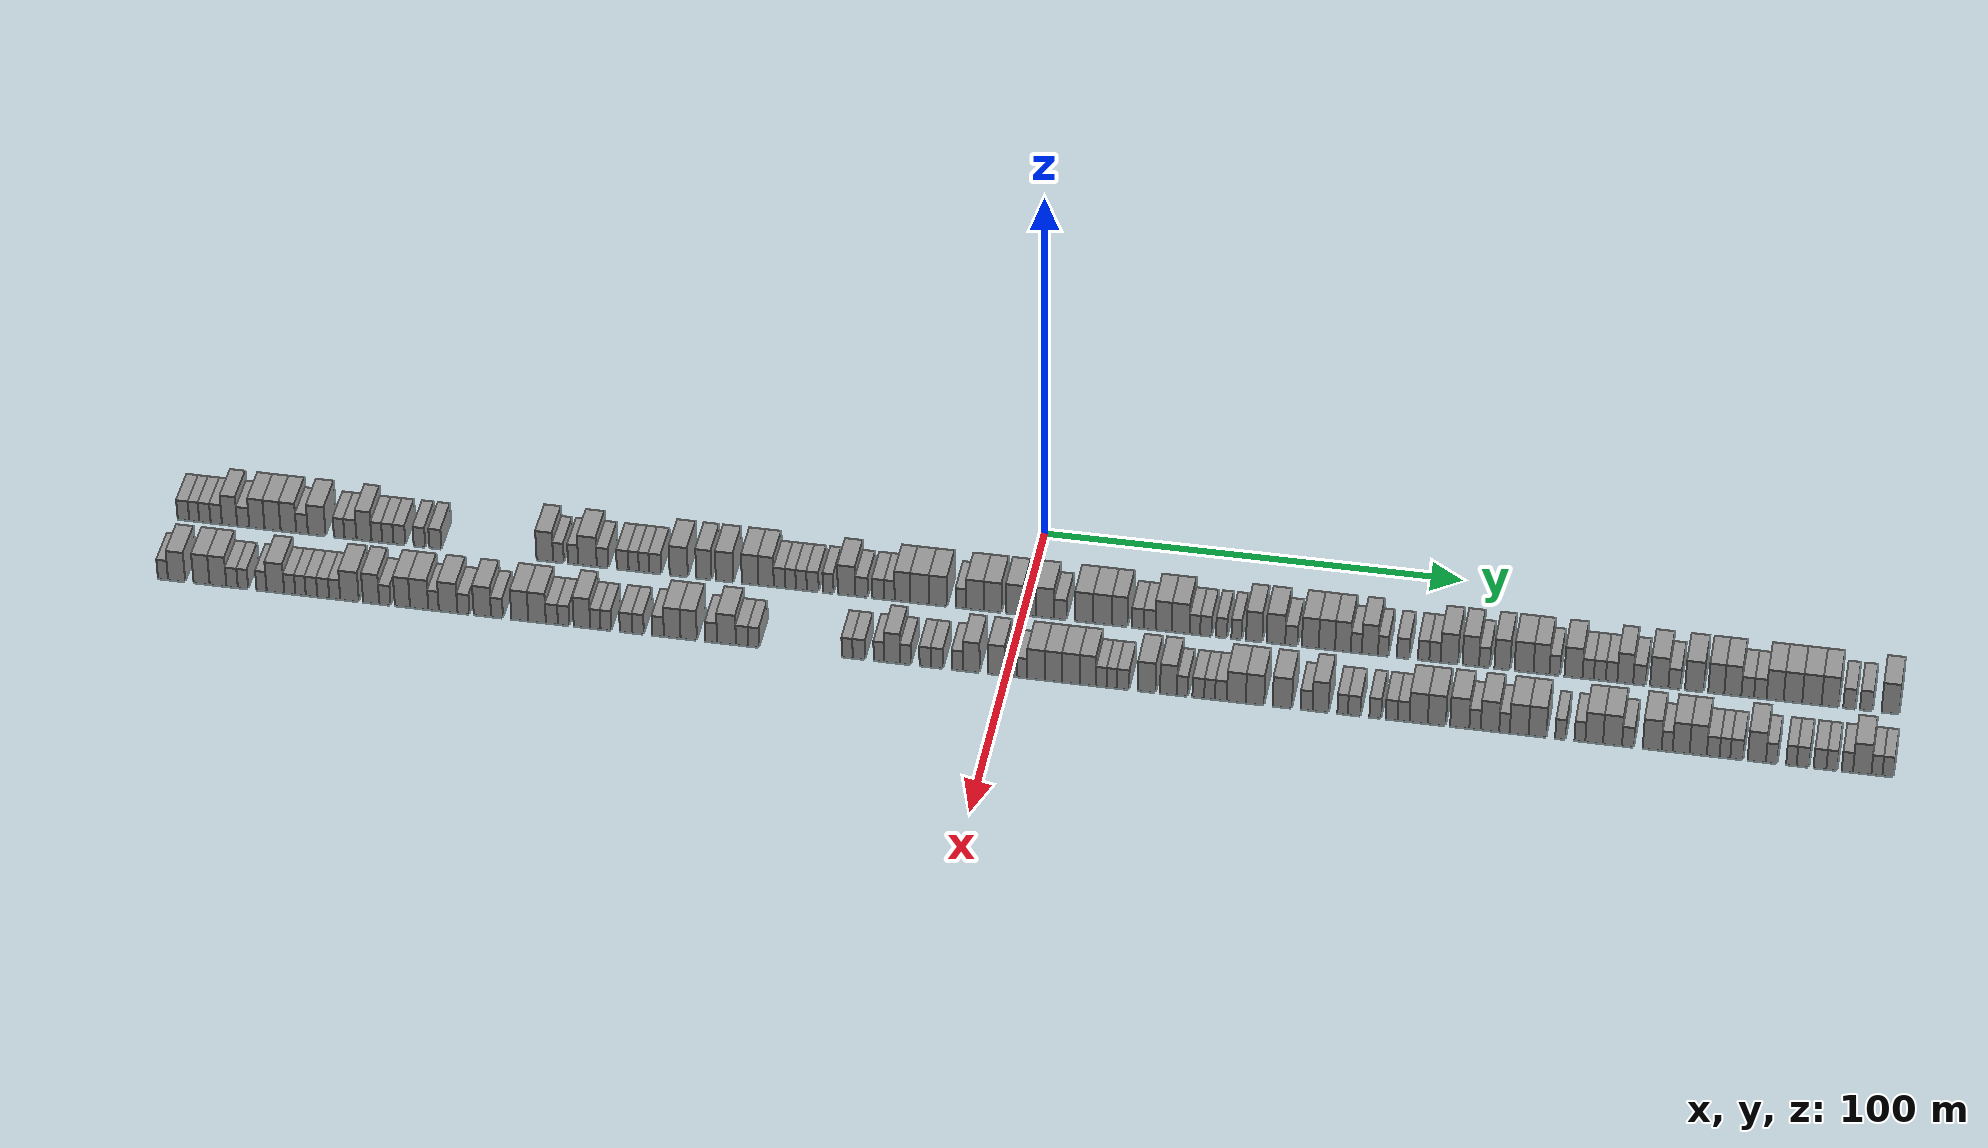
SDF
<sdf version="1.6">
 <world name="default">
  <scene>
   <sky><clouds><speed>12</speed></clouds></sky>
   <ambient>0.4 0.4 0.4 1</ambient>
   <background>0.7 0.7 0.7 1</background>
   <shadows>1</shadows>
  </scene>
  <gravity>0 0 -9.8066</gravity>
  <magnetic_field>6e-06 2.3e-05 -4.2e-05</magnetic_field>
  <physics default="0" name="default_physics" type="ode">
   <ode>
    <solver>
     <type>quick</type>
     <iters>10</iters>
     <sor>1.0</sor>
     <use_dynamic_moi_rescaling>0</use_dynamic_moi_rescaling>
    </solver>
    <constraints>
     <cfm>0</cfm>
     <erp>0.2</erp>
     <contact_max_correcting_vel>100</contact_max_correcting_vel>
     <contact_surface_layer>0.001</contact_surface_layer>
    </constraints>
   </ode>
   <max_step_size>0.004</max_step_size>
   <real_time_factor>1</real_time_factor>
   <real_time_update_rate>250</real_time_update_rate>
  </physics>
  <light name="sun" type="directional">
   <pose>0 0 10 0 0 0</pose>
   <diffuse>0.8 0.8 0.8 1</diffuse>
   <specular>0.2 0.2 0.2 1</specular>
   <attenuation>
    <range>1000</range>
    <constant>0.9</constant>
    <linear>0.01</linear>
    <quadratic>0.001</quadratic>
   </attenuation>
   <direction>-0.5 0.1 -0.9</direction>
  </light>
  <model name="building_1">
   <static>1</static>
   <pose>25.0000 -202.5751 0 0.000000 0.000000 0.000000</pose>
   <link name="link">
    <pose>0 0 3.00 0 0 0</pose>
    <collision name="collision"><geometry><box><size>10.0000 2.8498 6.0000</size></box></geometry></collision>
    <visual name="visual">
     <cast_shadows>0</cast_shadows>
     <geometry><box><size>10.0000 2.8498 6.0000</size></box></geometry>
     <material>
      <script>
       <uri>model://grey_wall/materials/scripts</uri>
       <uri>model://grey_wall/materials/textures</uri>
       <name>vrc/grey_wall</name>
      </script>
     </material>
    </visual>
   </link>
  </model>
  <model name="building_2">
   <static>1</static>
   <pose>25.0000 -199.9320 0 0.000000 0.000000 0.000000</pose>
   <link name="link">
    <pose>0 0 3.00 0 0 0</pose>
    <collision name="collision"><geometry><box><size>10.0000 2.4364 6.0000</size></box></geometry></collision>
    <visual name="visual">
     <cast_shadows>0</cast_shadows>
     <geometry><box><size>10.0000 2.4364 6.0000</size></box></geometry>
     <material>
      <script>
       <uri>model://grey_wall/materials/scripts</uri>
       <uri>model://grey_wall/materials/textures</uri>
       <name>vrc/grey_wall</name>
      </script>
     </material>
    </visual>
   </link>
  </model>
  <model name="building_3">
   <static>1</static>
   <pose>25.0000 -197.3201 0 0.000000 0.000000 0.000000</pose>
   <link name="link">
    <pose>0 0 3.00 0 0 0</pose>
    <collision name="collision"><geometry><box><size>10.0000 2.7874 6.0000</size></box></geometry></collision>
    <visual name="visual">
     <cast_shadows>0</cast_shadows>
     <geometry><box><size>10.0000 2.7874 6.0000</size></box></geometry>
     <material>
      <script>
       <uri>model://grey_wall/materials/scripts</uri>
       <uri>model://grey_wall/materials/textures</uri>
       <name>vrc/grey_wall</name>
      </script>
     </material>
    </visual>
   </link>
  </model>
  <model name="building_4">
   <static>1</static>
   <pose>25.0000 -194.5444 0 0.000000 0.000000 0.000000</pose>
   <link name="link">
    <pose>0 0 3.00 0 0 0</pose>
    <collision name="collision"><geometry><box><size>10.0000 2.7641 6.0000</size></box></geometry></collision>
    <visual name="visual">
     <cast_shadows>0</cast_shadows>
     <geometry><box><size>10.0000 2.7641 6.0000</size></box></geometry>
     <material>
      <script>
       <uri>model://grey_wall/materials/scripts</uri>
       <uri>model://grey_wall/materials/textures</uri>
       <name>vrc/grey_wall</name>
      </script>
     </material>
    </visual>
   </link>
  </model>
  <model name="building_5">
   <static>1</static>
   <pose>25.0000 -191.2901 0 0.000000 0.000000 0.000000</pose>
   <link name="link">
    <pose>0 0 4.50 0 0 0</pose>
    <collision name="collision"><geometry><box><size>10.0000 3.7444 9.0000</size></box></geometry></collision>
    <visual name="visual">
     <cast_shadows>0</cast_shadows>
     <geometry><box><size>10.0000 3.7444 9.0000</size></box></geometry>
     <material>
      <script>
       <uri>model://grey_wall/materials/scripts</uri>
       <uri>model://grey_wall/materials/textures</uri>
       <name>vrc/grey_wall</name>
      </script>
     </material>
    </visual>
   </link>
  </model>
  <model name="building_6">
   <static>1</static>
   <pose>25.0000 -187.9427 0 0.000000 0.000000 0.000000</pose>
   <link name="link">
    <pose>0 0 3.00 0 0 0</pose>
    <collision name="collision"><geometry><box><size>10.0000 2.9504 6.0000</size></box></geometry></collision>
    <visual name="visual">
     <cast_shadows>0</cast_shadows>
     <geometry><box><size>10.0000 2.9504 6.0000</size></box></geometry>
     <material>
      <script>
       <uri>model://grey_wall/materials/scripts</uri>
       <uri>model://grey_wall/materials/textures</uri>
       <name>vrc/grey_wall</name>
      </script>
     </material>
    </visual>
   </link>
  </model>
  <model name="building_7">
   <static>1</static>
   <pose>25.0000 -184.6122 0 0.000000 0.000000 0.000000</pose>
   <link name="link">
    <pose>0 0 4.50 0 0 0</pose>
    <collision name="collision"><geometry><box><size>10.0000 3.7106 9.0000</size></box></geometry></collision>
    <visual name="visual">
     <cast_shadows>0</cast_shadows>
     <geometry><box><size>10.0000 3.7106 9.0000</size></box></geometry>
     <material>
      <script>
       <uri>model://grey_wall/materials/scripts</uri>
       <uri>model://grey_wall/materials/textures</uri>
       <name>vrc/grey_wall</name>
      </script>
     </material>
    </visual>
   </link>
  </model>
  <model name="building_8">
   <static>1</static>
   <pose>25.0000 -180.7987 0 0.000000 0.000000 0.000000</pose>
   <link name="link">
    <pose>0 0 4.50 0 0 0</pose>
    <collision name="collision"><geometry><box><size>10.0000 3.9165 9.0000</size></box></geometry></collision>
    <visual name="visual">
     <cast_shadows>0</cast_shadows>
     <geometry><box><size>10.0000 3.9165 9.0000</size></box></geometry>
     <material>
      <script>
       <uri>model://grey_wall/materials/scripts</uri>
       <uri>model://grey_wall/materials/textures</uri>
       <name>vrc/grey_wall</name>
      </script>
     </material>
    </visual>
   </link>
  </model>
  <model name="building_9">
   <static>1</static>
   <pose>25.0000 -176.9204 0 0.000000 0.000000 0.000000</pose>
   <link name="link">
    <pose>0 0 4.50 0 0 0</pose>
    <collision name="collision"><geometry><box><size>10.0000 3.8401 9.0000</size></box></geometry></collision>
    <visual name="visual">
     <cast_shadows>0</cast_shadows>
     <geometry><box><size>10.0000 3.8401 9.0000</size></box></geometry>
     <material>
      <script>
       <uri>model://grey_wall/materials/scripts</uri>
       <uri>model://grey_wall/materials/textures</uri>
       <name>vrc/grey_wall</name>
      </script>
     </material>
    </visual>
   </link>
  </model>
  <model name="building_10">
   <static>1</static>
   <pose>25.0000 -173.5863 0 0.000000 0.000000 0.000000</pose>
   <link name="link">
    <pose>0 0 3.00 0 0 0</pose>
    <collision name="collision"><geometry><box><size>10.0000 2.8281 6.0000</size></box></geometry></collision>
    <visual name="visual">
     <cast_shadows>0</cast_shadows>
     <geometry><box><size>10.0000 2.8281 6.0000</size></box></geometry>
     <material>
      <script>
       <uri>model://grey_wall/materials/scripts</uri>
       <uri>model://grey_wall/materials/textures</uri>
       <name>vrc/grey_wall</name>
      </script>
     </material>
    </visual>
   </link>
  </model>
  <model name="building_11">
   <static>1</static>
   <pose>25.0000 -170.0081 0 0.000000 0.000000 0.000000</pose>
   <link name="link">
    <pose>0 0 4.50 0 0 0</pose>
    <collision name="collision"><geometry><box><size>10.0000 4.3283 9.0000</size></box></geometry></collision>
    <visual name="visual">
     <cast_shadows>0</cast_shadows>
     <geometry><box><size>10.0000 4.3283 9.0000</size></box></geometry>
     <material>
      <script>
       <uri>model://grey_wall/materials/scripts</uri>
       <uri>model://grey_wall/materials/textures</uri>
       <name>vrc/grey_wall</name>
      </script>
     </material>
    </visual>
   </link>
  </model>
  <model name="building_12">
   <static>1</static>
   <pose>25.0000 -164.5643 0 0.000000 0.000000 0.000000</pose>
   <link name="link">
    <pose>0 0 3.00 0 0 0</pose>
    <collision name="collision"><geometry><box><size>10.0000 2.5592 6.0000</size></box></geometry></collision>
    <visual name="visual">
     <cast_shadows>0</cast_shadows>
     <geometry><box><size>10.0000 2.5592 6.0000</size></box></geometry>
     <material>
      <script>
       <uri>model://grey_wall/materials/scripts</uri>
       <uri>model://grey_wall/materials/textures</uri>
       <name>vrc/grey_wall</name>
      </script>
     </material>
    </visual>
   </link>
  </model>
  <model name="building_13">
   <static>1</static>
   <pose>25.0000 -161.8121 0 0.000000 0.000000 0.000000</pose>
   <link name="link">
    <pose>0 0 3.00 0 0 0</pose>
    <collision name="collision"><geometry><box><size>10.0000 2.9453 6.0000</size></box></geometry></collision>
    <visual name="visual">
     <cast_shadows>0</cast_shadows>
     <geometry><box><size>10.0000 2.9453 6.0000</size></box></geometry>
     <material>
      <script>
       <uri>model://grey_wall/materials/scripts</uri>
       <uri>model://grey_wall/materials/textures</uri>
       <name>vrc/grey_wall</name>
      </script>
     </material>
    </visual>
   </link>
  </model>
  <model name="building_14">
   <static>1</static>
   <pose>25.0000 -158.5109 0 0.000000 0.000000 0.000000</pose>
   <link name="link">
    <pose>0 0 4.50 0 0 0</pose>
    <collision name="collision"><geometry><box><size>10.0000 3.6571 9.0000</size></box></geometry></collision>
    <visual name="visual">
     <cast_shadows>0</cast_shadows>
     <geometry><box><size>10.0000 3.6571 9.0000</size></box></geometry>
     <material>
      <script>
       <uri>model://grey_wall/materials/scripts</uri>
       <uri>model://grey_wall/materials/textures</uri>
       <name>vrc/grey_wall</name>
      </script>
     </material>
    </visual>
   </link>
  </model>
  <model name="building_15">
   <static>1</static>
   <pose>25.0000 -155.3823 0 0.000000 0.000000 0.000000</pose>
   <link name="link">
    <pose>0 0 3.00 0 0 0</pose>
    <collision name="collision"><geometry><box><size>10.0000 2.6001 6.0000</size></box></geometry></collision>
    <visual name="visual">
     <cast_shadows>0</cast_shadows>
     <geometry><box><size>10.0000 2.6001 6.0000</size></box></geometry>
     <material>
      <script>
       <uri>model://grey_wall/materials/scripts</uri>
       <uri>model://grey_wall/materials/textures</uri>
       <name>vrc/grey_wall</name>
      </script>
     </material>
    </visual>
   </link>
  </model>
  <model name="building_16">
   <static>1</static>
   <pose>25.0000 -152.7136 0 0.000000 0.000000 0.000000</pose>
   <link name="link">
    <pose>0 0 3.00 0 0 0</pose>
    <collision name="collision"><geometry><box><size>10.0000 2.7374 6.0000</size></box></geometry></collision>
    <visual name="visual">
     <cast_shadows>0</cast_shadows>
     <geometry><box><size>10.0000 2.7374 6.0000</size></box></geometry>
     <material>
      <script>
       <uri>model://grey_wall/materials/scripts</uri>
       <uri>model://grey_wall/materials/textures</uri>
       <name>vrc/grey_wall</name>
      </script>
     </material>
    </visual>
   </link>
  </model>
  <model name="building_17">
   <static>1</static>
   <pose>25.0000 -149.9025 0 0.000000 0.000000 0.000000</pose>
   <link name="link">
    <pose>0 0 3.00 0 0 0</pose>
    <collision name="collision"><geometry><box><size>10.0000 2.8847 6.0000</size></box></geometry></collision>
    <visual name="visual">
     <cast_shadows>0</cast_shadows>
     <geometry><box><size>10.0000 2.8847 6.0000</size></box></geometry>
     <material>
      <script>
       <uri>model://grey_wall/materials/scripts</uri>
       <uri>model://grey_wall/materials/textures</uri>
       <name>vrc/grey_wall</name>
      </script>
     </material>
    </visual>
   </link>
  </model>
  <model name="building_18">
   <static>1</static>
   <pose>25.0000 -145.0434 0 0.000000 0.000000 0.000000</pose>
   <link name="link">
    <pose>0 0 3.00 0 0 0</pose>
    <collision name="collision"><geometry><box><size>10.0000 2.8335 6.0000</size></box></geometry></collision>
    <visual name="visual">
     <cast_shadows>0</cast_shadows>
     <geometry><box><size>10.0000 2.8335 6.0000</size></box></geometry>
     <material>
      <script>
       <uri>model://grey_wall/materials/scripts</uri>
       <uri>model://grey_wall/materials/textures</uri>
       <name>vrc/grey_wall</name>
      </script>
     </material>
    </visual>
   </link>
  </model>
  <model name="building_19">
   <static>1</static>
   <pose>25.0000 -141.1644 0 0.000000 0.000000 0.000000</pose>
   <link name="link">
    <pose>0 0 3.00 0 0 0</pose>
    <collision name="collision"><geometry><box><size>10.0000 2.9245 6.0000</size></box></geometry></collision>
    <visual name="visual">
     <cast_shadows>0</cast_shadows>
     <geometry><box><size>10.0000 2.9245 6.0000</size></box></geometry>
     <material>
      <script>
       <uri>model://grey_wall/materials/scripts</uri>
       <uri>model://grey_wall/materials/textures</uri>
       <name>vrc/grey_wall</name>
      </script>
     </material>
    </visual>
   </link>
  </model>
  <model name="building_20">
   <static>1</static>
   <pose>25.0000 -114.6711 0 0.000000 0.000000 0.000000</pose>
   <link name="link">
    <pose>0 0 4.50 0 0 0</pose>
    <collision name="collision"><geometry><box><size>10.0000 4.0207 9.0000</size></box></geometry></collision>
    <visual name="visual">
     <cast_shadows>0</cast_shadows>
     <geometry><box><size>10.0000 4.0207 9.0000</size></box></geometry>
     <material>
      <script>
       <uri>model://grey_wall/materials/scripts</uri>
       <uri>model://grey_wall/materials/textures</uri>
       <name>vrc/grey_wall</name>
      </script>
     </material>
    </visual>
   </link>
  </model>
  <model name="building_21">
   <static>1</static>
   <pose>25.0000 -111.3727 0 0.000000 0.000000 0.000000</pose>
   <link name="link">
    <pose>0 0 3.00 0 0 0</pose>
    <collision name="collision"><geometry><box><size>10.0000 2.5760 6.0000</size></box></geometry></collision>
    <visual name="visual">
     <cast_shadows>0</cast_shadows>
     <geometry><box><size>10.0000 2.5760 6.0000</size></box></geometry>
     <material>
      <script>
       <uri>model://grey_wall/materials/scripts</uri>
       <uri>model://grey_wall/materials/textures</uri>
       <name>vrc/grey_wall</name>
      </script>
     </material>
    </visual>
   </link>
  </model>
  <model name="building_22">
   <static>1</static>
   <pose>25.0000 -107.8508 0 0.000000 0.000000 0.000000</pose>
   <link name="link">
    <pose>0 0 3.00 0 0 0</pose>
    <collision name="collision"><geometry><box><size>10.0000 2.4678 6.0000</size></box></geometry></collision>
    <visual name="visual">
     <cast_shadows>0</cast_shadows>
     <geometry><box><size>10.0000 2.4678 6.0000</size></box></geometry>
     <material>
      <script>
       <uri>model://grey_wall/materials/scripts</uri>
       <uri>model://grey_wall/materials/textures</uri>
       <name>vrc/grey_wall</name>
      </script>
     </material>
    </visual>
   </link>
  </model>
  <model name="building_23">
   <static>1</static>
   <pose>25.0000 -104.3762 0 0.000000 0.000000 0.000000</pose>
   <link name="link">
    <pose>0 0 4.50 0 0 0</pose>
    <collision name="collision"><geometry><box><size>10.0000 4.4815 9.0000</size></box></geometry></collision>
    <visual name="visual">
     <cast_shadows>0</cast_shadows>
     <geometry><box><size>10.0000 4.4815 9.0000</size></box></geometry>
     <material>
      <script>
       <uri>model://grey_wall/materials/scripts</uri>
       <uri>model://grey_wall/materials/textures</uri>
       <name>vrc/grey_wall</name>
      </script>
     </material>
    </visual>
   </link>
  </model>
  <model name="building_24">
   <static>1</static>
   <pose>25.0000 -100.7256 0 0.000000 0.000000 0.000000</pose>
   <link name="link">
    <pose>0 0 3.00 0 0 0</pose>
    <collision name="collision"><geometry><box><size>10.0000 2.8197 6.0000</size></box></geometry></collision>
    <visual name="visual">
     <cast_shadows>0</cast_shadows>
     <geometry><box><size>10.0000 2.8197 6.0000</size></box></geometry>
     <material>
      <script>
       <uri>model://grey_wall/materials/scripts</uri>
       <uri>model://grey_wall/materials/textures</uri>
       <name>vrc/grey_wall</name>
      </script>
     </material>
    </visual>
   </link>
  </model>
  <model name="building_25">
   <static>1</static>
   <pose>25.0000 -95.8948 0 0.000000 0.000000 0.000000</pose>
   <link name="link">
    <pose>0 0 3.00 0 0 0</pose>
    <collision name="collision"><geometry><box><size>10.0000 2.8417 6.0000</size></box></geometry></collision>
    <visual name="visual">
     <cast_shadows>0</cast_shadows>
     <geometry><box><size>10.0000 2.8417 6.0000</size></box></geometry>
     <material>
      <script>
       <uri>model://grey_wall/materials/scripts</uri>
       <uri>model://grey_wall/materials/textures</uri>
       <name>vrc/grey_wall</name>
      </script>
     </material>
    </visual>
   </link>
  </model>
  <model name="building_26">
   <static>1</static>
   <pose>25.0000 -93.2428 0 0.000000 0.000000 0.000000</pose>
   <link name="link">
    <pose>0 0 3.00 0 0 0</pose>
    <collision name="collision"><geometry><box><size>10.0000 2.4623 6.0000</size></box></geometry></collision>
    <visual name="visual">
     <cast_shadows>0</cast_shadows>
     <geometry><box><size>10.0000 2.4623 6.0000</size></box></geometry>
     <material>
      <script>
       <uri>model://grey_wall/materials/scripts</uri>
       <uri>model://grey_wall/materials/textures</uri>
       <name>vrc/grey_wall</name>
      </script>
     </material>
    </visual>
   </link>
  </model>
  <model name="building_27">
   <static>1</static>
   <pose>25.0000 -90.7668 0 0.000000 0.000000 0.000000</pose>
   <link name="link">
    <pose>0 0 3.00 0 0 0</pose>
    <collision name="collision"><geometry><box><size>10.0000 2.4897 6.0000</size></box></geometry></collision>
    <visual name="visual">
     <cast_shadows>0</cast_shadows>
     <geometry><box><size>10.0000 2.4897 6.0000</size></box></geometry>
     <material>
      <script>
       <uri>model://grey_wall/materials/scripts</uri>
       <uri>model://grey_wall/materials/textures</uri>
       <name>vrc/grey_wall</name>
      </script>
     </material>
    </visual>
   </link>
  </model>
  <model name="building_28">
   <static>1</static>
   <pose>25.0000 -88.0541 0 0.000000 0.000000 0.000000</pose>
   <link name="link">
    <pose>0 0 3.00 0 0 0</pose>
    <collision name="collision"><geometry><box><size>10.0000 2.9357 6.0000</size></box></geometry></collision>
    <visual name="visual">
     <cast_shadows>0</cast_shadows>
     <geometry><box><size>10.0000 2.9357 6.0000</size></box></geometry>
     <material>
      <script>
       <uri>model://grey_wall/materials/scripts</uri>
       <uri>model://grey_wall/materials/textures</uri>
       <name>vrc/grey_wall</name>
      </script>
     </material>
    </visual>
   </link>
  </model>
  <model name="building_29">
   <static>1</static>
   <pose>25.0000 -82.3936 0 0.000000 0.000000 0.000000</pose>
   <link name="link">
    <pose>0 0 4.50 0 0 0</pose>
    <collision name="collision"><geometry><box><size>10.0000 4.3852 9.0000</size></box></geometry></collision>
    <visual name="visual">
     <cast_shadows>0</cast_shadows>
     <geometry><box><size>10.0000 4.3852 9.0000</size></box></geometry>
     <material>
      <script>
       <uri>model://grey_wall/materials/scripts</uri>
       <uri>model://grey_wall/materials/textures</uri>
       <name>vrc/grey_wall</name>
      </script>
     </material>
    </visual>
   </link>
  </model>
  <model name="building_30">
   <static>1</static>
   <pose>25.0000 -76.3492 0 0.000000 0.000000 0.000000</pose>
   <link name="link">
    <pose>0 0 4.50 0 0 0</pose>
    <collision name="collision"><geometry><box><size>10.0000 3.7037 9.0000</size></box></geometry></collision>
    <visual name="visual">
     <cast_shadows>0</cast_shadows>
     <geometry><box><size>10.0000 3.7037 9.0000</size></box></geometry>
     <material>
      <script>
       <uri>model://grey_wall/materials/scripts</uri>
       <uri>model://grey_wall/materials/textures</uri>
       <name>vrc/grey_wall</name>
      </script>
     </material>
    </visual>
   </link>
  </model>
  <model name="building_31">
   <static>1</static>
   <pose>25.0000 -71.3695 0 0.000000 0.000000 0.000000</pose>
   <link name="link">
    <pose>0 0 4.50 0 0 0</pose>
    <collision name="collision"><geometry><box><size>10.0000 4.2556 9.0000</size></box></geometry></collision>
    <visual name="visual">
     <cast_shadows>0</cast_shadows>
     <geometry><box><size>10.0000 4.2556 9.0000</size></box></geometry>
     <material>
      <script>
       <uri>model://grey_wall/materials/scripts</uri>
       <uri>model://grey_wall/materials/textures</uri>
       <name>vrc/grey_wall</name>
      </script>
     </material>
    </visual>
   </link>
  </model>
  <model name="building_32">
   <static>1</static>
   <pose>25.0000 -65.2629 0 0.000000 0.000000 0.000000</pose>
   <link name="link">
    <pose>0 0 4.50 0 0 0</pose>
    <collision name="collision"><geometry><box><size>10.0000 3.9575 9.0000</size></box></geometry></collision>
    <visual name="visual">
     <cast_shadows>0</cast_shadows>
     <geometry><box><size>10.0000 3.9575 9.0000</size></box></geometry>
     <material>
      <script>
       <uri>model://grey_wall/materials/scripts</uri>
       <uri>model://grey_wall/materials/textures</uri>
       <name>vrc/grey_wall</name>
      </script>
     </material>
    </visual>
   </link>
  </model>
  <model name="building_33">
   <static>1</static>
   <pose>25.0000 -61.4327 0 0.000000 0.000000 0.000000</pose>
   <link name="link">
    <pose>0 0 4.50 0 0 0</pose>
    <collision name="collision"><geometry><box><size>10.0000 3.7027 9.0000</size></box></geometry></collision>
    <visual name="visual">
     <cast_shadows>0</cast_shadows>
     <geometry><box><size>10.0000 3.7027 9.0000</size></box></geometry>
     <material>
      <script>
       <uri>model://grey_wall/materials/scripts</uri>
       <uri>model://grey_wall/materials/textures</uri>
       <name>vrc/grey_wall</name>
      </script>
     </material>
    </visual>
   </link>
  </model>
  <model name="building_34">
   <static>1</static>
   <pose>25.0000 -58.2238 0 0.000000 0.000000 0.000000</pose>
   <link name="link">
    <pose>0 0 3.00 0 0 0</pose>
    <collision name="collision"><geometry><box><size>10.0000 2.7151 6.0000</size></box></geometry></collision>
    <visual name="visual">
     <cast_shadows>0</cast_shadows>
     <geometry><box><size>10.0000 2.7151 6.0000</size></box></geometry>
     <material>
      <script>
       <uri>model://grey_wall/materials/scripts</uri>
       <uri>model://grey_wall/materials/textures</uri>
       <name>vrc/grey_wall</name>
      </script>
     </material>
    </visual>
   </link>
  </model>
  <model name="building_35">
   <static>1</static>
   <pose>25.0000 -55.5876 0 0.000000 0.000000 0.000000</pose>
   <link name="link">
    <pose>0 0 3.00 0 0 0</pose>
    <collision name="collision"><geometry><box><size>10.0000 2.5574 6.0000</size></box></geometry></collision>
    <visual name="visual">
     <cast_shadows>0</cast_shadows>
     <geometry><box><size>10.0000 2.5574 6.0000</size></box></geometry>
     <material>
      <script>
       <uri>model://grey_wall/materials/scripts</uri>
       <uri>model://grey_wall/materials/textures</uri>
       <name>vrc/grey_wall</name>
      </script>
     </material>
    </visual>
   </link>
  </model>
  <model name="building_36">
   <static>1</static>
   <pose>25.0000 -53.0013 0 0.000000 0.000000 0.000000</pose>
   <link name="link">
    <pose>0 0 3.00 0 0 0</pose>
    <collision name="collision"><geometry><box><size>10.0000 2.6151 6.0000</size></box></geometry></collision>
    <visual name="visual">
     <cast_shadows>0</cast_shadows>
     <geometry><box><size>10.0000 2.6151 6.0000</size></box></geometry>
     <material>
      <script>
       <uri>model://grey_wall/materials/scripts</uri>
       <uri>model://grey_wall/materials/textures</uri>
       <name>vrc/grey_wall</name>
      </script>
     </material>
    </visual>
   </link>
  </model>
  <model name="building_37">
   <static>1</static>
   <pose>25.0000 -50.2593 0 0.000000 0.000000 0.000000</pose>
   <link name="link">
    <pose>0 0 3.00 0 0 0</pose>
    <collision name="collision"><geometry><box><size>10.0000 2.8688 6.0000</size></box></geometry></collision>
    <visual name="visual">
     <cast_shadows>0</cast_shadows>
     <geometry><box><size>10.0000 2.8688 6.0000</size></box></geometry>
     <material>
      <script>
       <uri>model://grey_wall/materials/scripts</uri>
       <uri>model://grey_wall/materials/textures</uri>
       <name>vrc/grey_wall</name>
      </script>
     </material>
    </visual>
   </link>
  </model>
  <model name="building_38">
   <static>1</static>
   <pose>25.0000 -46.5412 0 0.000000 0.000000 0.000000</pose>
   <link name="link">
    <pose>0 0 3.00 0 0 0</pose>
    <collision name="collision"><geometry><box><size>10.0000 2.5675 6.0000</size></box></geometry></collision>
    <visual name="visual">
     <cast_shadows>0</cast_shadows>
     <geometry><box><size>10.0000 2.5675 6.0000</size></box></geometry>
     <material>
      <script>
       <uri>model://grey_wall/materials/scripts</uri>
       <uri>model://grey_wall/materials/textures</uri>
       <name>vrc/grey_wall</name>
      </script>
     </material>
    </visual>
   </link>
  </model>
  <model name="building_39">
   <static>1</static>
   <pose>25.0000 -42.1483 0 0.000000 0.000000 0.000000</pose>
   <link name="link">
    <pose>0 0 4.50 0 0 0</pose>
    <collision name="collision"><geometry><box><size>10.0000 4.2184 9.0000</size></box></geometry></collision>
    <visual name="visual">
     <cast_shadows>0</cast_shadows>
     <geometry><box><size>10.0000 4.2184 9.0000</size></box></geometry>
     <material>
      <script>
       <uri>model://grey_wall/materials/scripts</uri>
       <uri>model://grey_wall/materials/textures</uri>
       <name>vrc/grey_wall</name>
      </script>
     </material>
    </visual>
   </link>
  </model>
  <model name="building_40">
   <static>1</static>
   <pose>25.0000 -38.5617 0 0.000000 0.000000 0.000000</pose>
   <link name="link">
    <pose>0 0 3.00 0 0 0</pose>
    <collision name="collision"><geometry><box><size>10.0000 2.9548 6.0000</size></box></geometry></collision>
    <visual name="visual">
     <cast_shadows>0</cast_shadows>
     <geometry><box><size>10.0000 2.9548 6.0000</size></box></geometry>
     <material>
      <script>
       <uri>model://grey_wall/materials/scripts</uri>
       <uri>model://grey_wall/materials/textures</uri>
       <name>vrc/grey_wall</name>
      </script>
     </material>
    </visual>
   </link>
  </model>
  <model name="building_41">
   <static>1</static>
   <pose>25.0000 -34.5960 0 0.000000 0.000000 0.000000</pose>
   <link name="link">
    <pose>0 0 3.00 0 0 0</pose>
    <collision name="collision"><geometry><box><size>10.0000 2.9766 6.0000</size></box></geometry></collision>
    <visual name="visual">
     <cast_shadows>0</cast_shadows>
     <geometry><box><size>10.0000 2.9766 6.0000</size></box></geometry>
     <material>
      <script>
       <uri>model://grey_wall/materials/scripts</uri>
       <uri>model://grey_wall/materials/textures</uri>
       <name>vrc/grey_wall</name>
      </script>
     </material>
    </visual>
   </link>
  </model>
  <model name="building_42">
   <static>1</static>
   <pose>25.0000 -31.8885 0 0.000000 0.000000 0.000000</pose>
   <link name="link">
    <pose>0 0 3.00 0 0 0</pose>
    <collision name="collision"><geometry><box><size>10.0000 2.4384 6.0000</size></box></geometry></collision>
    <visual name="visual">
     <cast_shadows>0</cast_shadows>
     <geometry><box><size>10.0000 2.4384 6.0000</size></box></geometry>
     <material>
      <script>
       <uri>model://grey_wall/materials/scripts</uri>
       <uri>model://grey_wall/materials/textures</uri>
       <name>vrc/grey_wall</name>
      </script>
     </material>
    </visual>
   </link>
  </model>
  <model name="building_43">
   <static>1</static>
   <pose>25.0000 -28.7866 0 0.000000 0.000000 0.000000</pose>
   <link name="link">
    <pose>0 0 4.50 0 0 0</pose>
    <collision name="collision"><geometry><box><size>10.0000 3.7654 9.0000</size></box></geometry></collision>
    <visual name="visual">
     <cast_shadows>0</cast_shadows>
     <geometry><box><size>10.0000 3.7654 9.0000</size></box></geometry>
     <material>
      <script>
       <uri>model://grey_wall/materials/scripts</uri>
       <uri>model://grey_wall/materials/textures</uri>
       <name>vrc/grey_wall</name>
      </script>
     </material>
    </visual>
   </link>
  </model>
  <model name="building_44">
   <static>1</static>
   <pose>25.0000 -24.6649 0 0.000000 0.000000 0.000000</pose>
   <link name="link">
    <pose>0 0 4.50 0 0 0</pose>
    <collision name="collision"><geometry><box><size>10.0000 4.4779 9.0000</size></box></geometry></collision>
    <visual name="visual">
     <cast_shadows>0</cast_shadows>
     <geometry><box><size>10.0000 4.4779 9.0000</size></box></geometry>
     <material>
      <script>
       <uri>model://grey_wall/materials/scripts</uri>
       <uri>model://grey_wall/materials/textures</uri>
       <name>vrc/grey_wall</name>
      </script>
     </material>
    </visual>
   </link>
  </model>
  <model name="building_45">
   <static>1</static>
   <pose>25.0000 -20.2596 0 0.000000 0.000000 0.000000</pose>
   <link name="link">
    <pose>0 0 4.50 0 0 0</pose>
    <collision name="collision"><geometry><box><size>10.0000 4.3327 9.0000</size></box></geometry></collision>
    <visual name="visual">
     <cast_shadows>0</cast_shadows>
     <geometry><box><size>10.0000 4.3327 9.0000</size></box></geometry>
     <material>
      <script>
       <uri>model://grey_wall/materials/scripts</uri>
       <uri>model://grey_wall/materials/textures</uri>
       <name>vrc/grey_wall</name>
      </script>
     </material>
    </visual>
   </link>
  </model>
  <model name="building_46">
   <static>1</static>
   <pose>25.0000 -14.8365 0 0.000000 0.000000 0.000000</pose>
   <link name="link">
    <pose>0 0 3.00 0 0 0</pose>
    <collision name="collision"><geometry><box><size>10.0000 2.5137 6.0000</size></box></geometry></collision>
    <visual name="visual">
     <cast_shadows>0</cast_shadows>
     <geometry><box><size>10.0000 2.5137 6.0000</size></box></geometry>
     <material>
      <script>
       <uri>model://grey_wall/materials/scripts</uri>
       <uri>model://grey_wall/materials/textures</uri>
       <name>vrc/grey_wall</name>
      </script>
     </material>
    </visual>
   </link>
  </model>
  <model name="building_47">
   <static>1</static>
   <pose>25.0000 -11.5016 0 0.000000 0.000000 0.000000</pose>
   <link name="link">
    <pose>0 0 4.50 0 0 0</pose>
    <collision name="collision"><geometry><box><size>10.0000 4.1561 9.0000</size></box></geometry></collision>
    <visual name="visual">
     <cast_shadows>0</cast_shadows>
     <geometry><box><size>10.0000 4.1561 9.0000</size></box></geometry>
     <material>
      <script>
       <uri>model://grey_wall/materials/scripts</uri>
       <uri>model://grey_wall/materials/textures</uri>
       <name>vrc/grey_wall</name>
      </script>
     </material>
    </visual>
   </link>
  </model>
  <model name="building_48">
   <static>1</static>
   <pose>25.0000 -7.2964 0 0.000000 0.000000 0.000000</pose>
   <link name="link">
    <pose>0 0 4.50 0 0 0</pose>
    <collision name="collision"><geometry><box><size>10.0000 4.2544 9.0000</size></box></geometry></collision>
    <visual name="visual">
     <cast_shadows>0</cast_shadows>
     <geometry><box><size>10.0000 4.2544 9.0000</size></box></geometry>
     <material>
      <script>
       <uri>model://grey_wall/materials/scripts</uri>
       <uri>model://grey_wall/materials/textures</uri>
       <name>vrc/grey_wall</name>
      </script>
     </material>
    </visual>
   </link>
  </model>
  <model name="building_49">
   <static>1</static>
   <pose>25.0000 -2.0602 0 0.000000 0.000000 0.000000</pose>
   <link name="link">
    <pose>0 0 4.50 0 0 0</pose>
    <collision name="collision"><geometry><box><size>10.0000 4.2179 9.0000</size></box></geometry></collision>
    <visual name="visual">
     <cast_shadows>0</cast_shadows>
     <geometry><box><size>10.0000 4.2179 9.0000</size></box></geometry>
     <material>
      <script>
       <uri>model://grey_wall/materials/scripts</uri>
       <uri>model://grey_wall/materials/textures</uri>
       <name>vrc/grey_wall</name>
      </script>
     </material>
    </visual>
   </link>
  </model>
  <model name="building_50">
   <static>1</static>
   <pose>25.0000 1.4626 0 0.000000 0.000000 0.000000</pose>
   <link name="link">
    <pose>0 0 3.00 0 0 0</pose>
    <collision name="collision"><geometry><box><size>10.0000 2.8276 6.0000</size></box></geometry></collision>
    <visual name="visual">
     <cast_shadows>0</cast_shadows>
     <geometry><box><size>10.0000 2.8276 6.0000</size></box></geometry>
     <material>
      <script>
       <uri>model://grey_wall/materials/scripts</uri>
       <uri>model://grey_wall/materials/textures</uri>
       <name>vrc/grey_wall</name>
      </script>
     </material>
    </visual>
   </link>
  </model>
  <model name="building_51">
   <static>1</static>
   <pose>25.0000 5.0964 0 0.000000 0.000000 0.000000</pose>
   <link name="link">
    <pose>0 0 4.50 0 0 0</pose>
    <collision name="collision"><geometry><box><size>10.0000 4.4400 9.0000</size></box></geometry></collision>
    <visual name="visual">
     <cast_shadows>0</cast_shadows>
     <geometry><box><size>10.0000 4.4400 9.0000</size></box></geometry>
     <material>
      <script>
       <uri>model://grey_wall/materials/scripts</uri>
       <uri>model://grey_wall/materials/textures</uri>
       <name>vrc/grey_wall</name>
      </script>
     </material>
    </visual>
   </link>
  </model>
  <model name="building_52">
   <static>1</static>
   <pose>25.0000 8.7997 0 0.000000 0.000000 0.000000</pose>
   <link name="link">
    <pose>0 0 3.00 0 0 0</pose>
    <collision name="collision"><geometry><box><size>10.0000 2.9665 6.0000</size></box></geometry></collision>
    <visual name="visual">
     <cast_shadows>0</cast_shadows>
     <geometry><box><size>10.0000 2.9665 6.0000</size></box></geometry>
     <material>
      <script>
       <uri>model://grey_wall/materials/scripts</uri>
       <uri>model://grey_wall/materials/textures</uri>
       <name>vrc/grey_wall</name>
      </script>
     </material>
    </visual>
   </link>
  </model>
  <model name="building_53">
   <static>1</static>
   <pose>25.0000 14.4339 0 0.000000 0.000000 0.000000</pose>
   <link name="link">
    <pose>0 0 4.50 0 0 0</pose>
    <collision name="collision"><geometry><box><size>10.0000 4.3020 9.0000</size></box></geometry></collision>
    <visual name="visual">
     <cast_shadows>0</cast_shadows>
     <geometry><box><size>10.0000 4.3020 9.0000</size></box></geometry>
     <material>
      <script>
       <uri>model://grey_wall/materials/scripts</uri>
       <uri>model://grey_wall/materials/textures</uri>
       <name>vrc/grey_wall</name>
      </script>
     </material>
    </visual>
   </link>
  </model>
  <model name="building_54">
   <static>1</static>
   <pose>25.0000 18.8188 0 0.000000 0.000000 0.000000</pose>
   <link name="link">
    <pose>0 0 4.50 0 0 0</pose>
    <collision name="collision"><geometry><box><size>10.0000 4.4679 9.0000</size></box></geometry></collision>
    <visual name="visual">
     <cast_shadows>0</cast_shadows>
     <geometry><box><size>10.0000 4.4679 9.0000</size></box></geometry>
     <material>
      <script>
       <uri>model://grey_wall/materials/scripts</uri>
       <uri>model://grey_wall/materials/textures</uri>
       <name>vrc/grey_wall</name>
      </script>
     </material>
    </visual>
   </link>
  </model>
  <model name="building_55">
   <static>1</static>
   <pose>25.0000 22.9044 0 0.000000 0.000000 0.000000</pose>
   <link name="link">
    <pose>0 0 4.50 0 0 0</pose>
    <collision name="collision"><geometry><box><size>10.0000 3.7032 9.0000</size></box></geometry></collision>
    <visual name="visual">
     <cast_shadows>0</cast_shadows>
     <geometry><box><size>10.0000 3.7032 9.0000</size></box></geometry>
     <material>
      <script>
       <uri>model://grey_wall/materials/scripts</uri>
       <uri>model://grey_wall/materials/textures</uri>
       <name>vrc/grey_wall</name>
      </script>
     </material>
    </visual>
   </link>
  </model>
  <model name="building_56">
   <static>1</static>
   <pose>25.0000 27.1491 0 0.000000 0.000000 0.000000</pose>
   <link name="link">
    <pose>0 0 3.00 0 0 0</pose>
    <collision name="collision"><geometry><box><size>10.0000 2.7863 6.0000</size></box></geometry></collision>
    <visual name="visual">
     <cast_shadows>0</cast_shadows>
     <geometry><box><size>10.0000 2.7863 6.0000</size></box></geometry>
     <material>
      <script>
       <uri>model://grey_wall/materials/scripts</uri>
       <uri>model://grey_wall/materials/textures</uri>
       <name>vrc/grey_wall</name>
      </script>
     </material>
    </visual>
   </link>
  </model>
  <model name="building_57">
   <static>1</static>
   <pose>25.0000 29.9320 0 0.000000 0.000000 0.000000</pose>
   <link name="link">
    <pose>0 0 3.00 0 0 0</pose>
    <collision name="collision"><geometry><box><size>10.0000 2.7795 6.0000</size></box></geometry></collision>
    <visual name="visual">
     <cast_shadows>0</cast_shadows>
     <geometry><box><size>10.0000 2.7795 6.0000</size></box></geometry>
     <material>
      <script>
       <uri>model://grey_wall/materials/scripts</uri>
       <uri>model://grey_wall/materials/textures</uri>
       <name>vrc/grey_wall</name>
      </script>
     </material>
    </visual>
   </link>
  </model>
  <model name="building_58">
   <static>1</static>
   <pose>25.0000 33.2780 0 0.000000 0.000000 0.000000</pose>
   <link name="link">
    <pose>0 0 4.50 0 0 0</pose>
    <collision name="collision"><geometry><box><size>10.0000 3.9124 9.0000</size></box></geometry></collision>
    <visual name="visual">
     <cast_shadows>0</cast_shadows>
     <geometry><box><size>10.0000 3.9124 9.0000</size></box></geometry>
     <material>
      <script>
       <uri>model://grey_wall/materials/scripts</uri>
       <uri>model://grey_wall/materials/textures</uri>
       <name>vrc/grey_wall</name>
      </script>
     </material>
    </visual>
   </link>
  </model>
  <model name="building_59">
   <static>1</static>
   <pose>25.0000 37.3160 0 0.000000 0.000000 0.000000</pose>
   <link name="link">
    <pose>0 0 4.50 0 0 0</pose>
    <collision name="collision"><geometry><box><size>10.0000 4.1636 9.0000</size></box></geometry></collision>
    <visual name="visual">
     <cast_shadows>0</cast_shadows>
     <geometry><box><size>10.0000 4.1636 9.0000</size></box></geometry>
     <material>
      <script>
       <uri>model://grey_wall/materials/scripts</uri>
       <uri>model://grey_wall/materials/textures</uri>
       <name>vrc/grey_wall</name>
      </script>
     </material>
    </visual>
   </link>
  </model>
  <model name="building_60">
   <static>1</static>
   <pose>25.0000 40.6521 0 0.000000 0.000000 0.000000</pose>
   <link name="link">
    <pose>0 0 3.00 0 0 0</pose>
    <collision name="collision"><geometry><box><size>10.0000 2.5086 6.0000</size></box></geometry></collision>
    <visual name="visual">
     <cast_shadows>0</cast_shadows>
     <geometry><box><size>10.0000 2.5086 6.0000</size></box></geometry>
     <material>
      <script>
       <uri>model://grey_wall/materials/scripts</uri>
       <uri>model://grey_wall/materials/textures</uri>
       <name>vrc/grey_wall</name>
      </script>
     </material>
    </visual>
   </link>
  </model>
  <model name="building_61">
   <static>1</static>
   <pose>25.0000 43.2868 0 0.000000 0.000000 0.000000</pose>
   <link name="link">
    <pose>0 0 3.00 0 0 0</pose>
    <collision name="collision"><geometry><box><size>10.0000 2.7609 6.0000</size></box></geometry></collision>
    <visual name="visual">
     <cast_shadows>0</cast_shadows>
     <geometry><box><size>10.0000 2.7609 6.0000</size></box></geometry>
     <material>
      <script>
       <uri>model://grey_wall/materials/scripts</uri>
       <uri>model://grey_wall/materials/textures</uri>
       <name>vrc/grey_wall</name>
      </script>
     </material>
    </visual>
   </link>
  </model>
  <model name="building_62">
   <static>1</static>
   <pose>25.0000 46.9627 0 0.000000 0.000000 0.000000</pose>
   <link name="link">
    <pose>0 0 3.00 0 0 0</pose>
    <collision name="collision"><geometry><box><size>10.0000 2.5908 6.0000</size></box></geometry></collision>
    <visual name="visual">
     <cast_shadows>0</cast_shadows>
     <geometry><box><size>10.0000 2.5908 6.0000</size></box></geometry>
     <material>
      <script>
       <uri>model://grey_wall/materials/scripts</uri>
       <uri>model://grey_wall/materials/textures</uri>
       <name>vrc/grey_wall</name>
      </script>
     </material>
    </visual>
   </link>
  </model>
  <model name="building_63">
   <static>1</static>
   <pose>25.0000 50.5032 0 0.000000 0.000000 0.000000</pose>
   <link name="link">
    <pose>0 0 3.00 0 0 0</pose>
    <collision name="collision"><geometry><box><size>10.0000 2.4901 6.0000</size></box></geometry></collision>
    <visual name="visual">
     <cast_shadows>0</cast_shadows>
     <geometry><box><size>10.0000 2.4901 6.0000</size></box></geometry>
     <material>
      <script>
       <uri>model://grey_wall/materials/scripts</uri>
       <uri>model://grey_wall/materials/textures</uri>
       <name>vrc/grey_wall</name>
      </script>
     </material>
    </visual>
   </link>
  </model>
  <model name="building_64">
   <static>1</static>
   <pose>25.0000 54.6744 0 0.000000 0.000000 0.000000</pose>
   <link name="link">
    <pose>0 0 4.50 0 0 0</pose>
    <collision name="collision"><geometry><box><size>10.0000 3.8524 9.0000</size></box></geometry></collision>
    <visual name="visual">
     <cast_shadows>0</cast_shadows>
     <geometry><box><size>10.0000 3.8524 9.0000</size></box></geometry>
     <material>
      <script>
       <uri>model://grey_wall/materials/scripts</uri>
       <uri>model://grey_wall/materials/textures</uri>
       <name>vrc/grey_wall</name>
      </script>
     </material>
    </visual>
   </link>
  </model>
  <model name="building_65">
   <static>1</static>
   <pose>25.0000 59.7795 0 0.000000 0.000000 0.000000</pose>
   <link name="link">
    <pose>0 0 4.50 0 0 0</pose>
    <collision name="collision"><geometry><box><size>10.0000 4.3577 9.0000</size></box></geometry></collision>
    <visual name="visual">
     <cast_shadows>0</cast_shadows>
     <geometry><box><size>10.0000 4.3577 9.0000</size></box></geometry>
     <material>
      <script>
       <uri>model://grey_wall/materials/scripts</uri>
       <uri>model://grey_wall/materials/textures</uri>
       <name>vrc/grey_wall</name>
      </script>
     </material>
    </visual>
   </link>
  </model>
  <model name="building_66">
   <static>1</static>
   <pose>25.0000 63.4287 0 0.000000 0.000000 0.000000</pose>
   <link name="link">
    <pose>0 0 3.00 0 0 0</pose>
    <collision name="collision"><geometry><box><size>10.0000 2.9407 6.0000</size></box></geometry></collision>
    <visual name="visual">
     <cast_shadows>0</cast_shadows>
     <geometry><box><size>10.0000 2.9407 6.0000</size></box></geometry>
     <material>
      <script>
       <uri>model://grey_wall/materials/scripts</uri>
       <uri>model://grey_wall/materials/textures</uri>
       <name>vrc/grey_wall</name>
      </script>
     </material>
    </visual>
   </link>
  </model>
  <model name="building_67">
   <static>1</static>
   <pose>25.0000 67.8861 0 0.000000 0.000000 0.000000</pose>
   <link name="link">
    <pose>0 0 4.50 0 0 0</pose>
    <collision name="collision"><geometry><box><size>10.0000 3.9743 9.0000</size></box></geometry></collision>
    <visual name="visual">
     <cast_shadows>0</cast_shadows>
     <geometry><box><size>10.0000 3.9743 9.0000</size></box></geometry>
     <material>
      <script>
       <uri>model://grey_wall/materials/scripts</uri>
       <uri>model://grey_wall/materials/textures</uri>
       <name>vrc/grey_wall</name>
      </script>
     </material>
    </visual>
   </link>
  </model>
  <model name="building_68">
   <static>1</static>
   <pose>25.0000 71.7823 0 0.000000 0.000000 0.000000</pose>
   <link name="link">
    <pose>0 0 4.50 0 0 0</pose>
    <collision name="collision"><geometry><box><size>10.0000 3.8181 9.0000</size></box></geometry></collision>
    <visual name="visual">
     <cast_shadows>0</cast_shadows>
     <geometry><box><size>10.0000 3.8181 9.0000</size></box></geometry>
     <material>
      <script>
       <uri>model://grey_wall/materials/scripts</uri>
       <uri>model://grey_wall/materials/textures</uri>
       <name>vrc/grey_wall</name>
      </script>
     </material>
    </visual>
   </link>
  </model>
  <model name="building_69">
   <static>1</static>
   <pose>25.0000 75.5488 0 0.000000 0.000000 0.000000</pose>
   <link name="link">
    <pose>0 0 4.50 0 0 0</pose>
    <collision name="collision"><geometry><box><size>10.0000 3.7149 9.0000</size></box></geometry></collision>
    <visual name="visual">
     <cast_shadows>0</cast_shadows>
     <geometry><box><size>10.0000 3.7149 9.0000</size></box></geometry>
     <material>
      <script>
       <uri>model://grey_wall/materials/scripts</uri>
       <uri>model://grey_wall/materials/textures</uri>
       <name>vrc/grey_wall</name>
      </script>
     </material>
    </visual>
   </link>
  </model>
  <model name="building_70">
   <static>1</static>
   <pose>25.0000 78.6993 0 0.000000 0.000000 0.000000</pose>
   <link name="link">
    <pose>0 0 3.00 0 0 0</pose>
    <collision name="collision"><geometry><box><size>10.0000 2.5861 6.0000</size></box></geometry></collision>
    <visual name="visual">
     <cast_shadows>0</cast_shadows>
     <geometry><box><size>10.0000 2.5861 6.0000</size></box></geometry>
     <material>
      <script>
       <uri>model://grey_wall/materials/scripts</uri>
       <uri>model://grey_wall/materials/textures</uri>
       <name>vrc/grey_wall</name>
      </script>
     </material>
    </visual>
   </link>
  </model>
  <model name="building_71">
   <static>1</static>
   <pose>25.0000 81.8857 0 0.000000 0.000000 0.000000</pose>
   <link name="link">
    <pose>0 0 4.50 0 0 0</pose>
    <collision name="collision"><geometry><box><size>10.0000 3.7866 9.0000</size></box></geometry></collision>
    <visual name="visual">
     <cast_shadows>0</cast_shadows>
     <geometry><box><size>10.0000 3.7866 9.0000</size></box></geometry>
     <material>
      <script>
       <uri>model://grey_wall/materials/scripts</uri>
       <uri>model://grey_wall/materials/textures</uri>
       <name>vrc/grey_wall</name>
      </script>
     </material>
    </visual>
   </link>
  </model>
  <model name="building_72">
   <static>1</static>
   <pose>25.0000 84.9985 0 0.000000 0.000000 0.000000</pose>
   <link name="link">
    <pose>0 0 3.00 0 0 0</pose>
    <collision name="collision"><geometry><box><size>10.0000 2.4390 6.0000</size></box></geometry></collision>
    <visual name="visual">
     <cast_shadows>0</cast_shadows>
     <geometry><box><size>10.0000 2.4390 6.0000</size></box></geometry>
     <material>
      <script>
       <uri>model://grey_wall/materials/scripts</uri>
       <uri>model://grey_wall/materials/textures</uri>
       <name>vrc/grey_wall</name>
      </script>
     </material>
    </visual>
   </link>
  </model>
  <model name="building_73">
   <static>1</static>
   <pose>25.0000 89.6909 0 0.000000 0.000000 0.000000</pose>
   <link name="link">
    <pose>0 0 3.00 0 0 0</pose>
    <collision name="collision"><geometry><box><size>10.0000 2.9460 6.0000</size></box></geometry></collision>
    <visual name="visual">
     <cast_shadows>0</cast_shadows>
     <geometry><box><size>10.0000 2.9460 6.0000</size></box></geometry>
     <material>
      <script>
       <uri>model://grey_wall/materials/scripts</uri>
       <uri>model://grey_wall/materials/textures</uri>
       <name>vrc/grey_wall</name>
      </script>
     </material>
    </visual>
   </link>
  </model>
  <model name="building_74">
   <static>1</static>
   <pose>25.0000 94.4838 0 0.000000 0.000000 0.000000</pose>
   <link name="link">
    <pose>0 0 3.00 0 0 0</pose>
    <collision name="collision"><geometry><box><size>10.0000 2.6397 6.0000</size></box></geometry></collision>
    <visual name="visual">
     <cast_shadows>0</cast_shadows>
     <geometry><box><size>10.0000 2.6397 6.0000</size></box></geometry>
     <material>
      <script>
       <uri>model://grey_wall/materials/scripts</uri>
       <uri>model://grey_wall/materials/textures</uri>
       <name>vrc/grey_wall</name>
      </script>
     </material>
    </visual>
   </link>
  </model>
  <model name="building_75">
   <static>1</static>
   <pose>25.0000 97.1282 0 0.000000 0.000000 0.000000</pose>
   <link name="link">
    <pose>0 0 3.00 0 0 0</pose>
    <collision name="collision"><geometry><box><size>10.0000 2.6492 6.0000</size></box></geometry></collision>
    <visual name="visual">
     <cast_shadows>0</cast_shadows>
     <geometry><box><size>10.0000 2.6492 6.0000</size></box></geometry>
     <material>
      <script>
       <uri>model://grey_wall/materials/scripts</uri>
       <uri>model://grey_wall/materials/textures</uri>
       <name>vrc/grey_wall</name>
      </script>
     </material>
    </visual>
   </link>
  </model>
  <model name="building_76">
   <static>1</static>
   <pose>25.0000 100.5202 0 0.000000 0.000000 0.000000</pose>
   <link name="link">
    <pose>0 0 4.50 0 0 0</pose>
    <collision name="collision"><geometry><box><size>10.0000 4.1348 9.0000</size></box></geometry></collision>
    <visual name="visual">
     <cast_shadows>0</cast_shadows>
     <geometry><box><size>10.0000 4.1348 9.0000</size></box></geometry>
     <material>
      <script>
       <uri>model://grey_wall/materials/scripts</uri>
       <uri>model://grey_wall/materials/textures</uri>
       <name>vrc/grey_wall</name>
      </script>
     </material>
    </visual>
   </link>
  </model>
  <model name="building_77">
   <static>1</static>
   <pose>25.0000 105.5133 0 0.000000 0.000000 0.000000</pose>
   <link name="link">
    <pose>0 0 4.50 0 0 0</pose>
    <collision name="collision"><geometry><box><size>10.0000 3.8513 9.0000</size></box></geometry></collision>
    <visual name="visual">
     <cast_shadows>0</cast_shadows>
     <geometry><box><size>10.0000 3.8513 9.0000</size></box></geometry>
     <material>
      <script>
       <uri>model://grey_wall/materials/scripts</uri>
       <uri>model://grey_wall/materials/textures</uri>
       <name>vrc/grey_wall</name>
      </script>
     </material>
    </visual>
   </link>
  </model>
  <model name="building_78">
   <static>1</static>
   <pose>25.0000 108.7378 0 0.000000 0.000000 0.000000</pose>
   <link name="link">
    <pose>0 0 3.00 0 0 0</pose>
    <collision name="collision"><geometry><box><size>10.0000 2.5978 6.0000</size></box></geometry></collision>
    <visual name="visual">
     <cast_shadows>0</cast_shadows>
     <geometry><box><size>10.0000 2.5978 6.0000</size></box></geometry>
     <material>
      <script>
       <uri>model://grey_wall/materials/scripts</uri>
       <uri>model://grey_wall/materials/textures</uri>
       <name>vrc/grey_wall</name>
      </script>
     </material>
    </visual>
   </link>
  </model>
  <model name="building_79">
   <static>1</static>
   <pose>25.0000 112.8844 0 0.000000 0.000000 0.000000</pose>
   <link name="link">
    <pose>0 0 4.50 0 0 0</pose>
    <collision name="collision"><geometry><box><size>10.0000 3.6953 9.0000</size></box></geometry></collision>
    <visual name="visual">
     <cast_shadows>0</cast_shadows>
     <geometry><box><size>10.0000 3.6953 9.0000</size></box></geometry>
     <material>
      <script>
       <uri>model://grey_wall/materials/scripts</uri>
       <uri>model://grey_wall/materials/textures</uri>
       <name>vrc/grey_wall</name>
      </script>
     </material>
    </visual>
   </link>
  </model>
  <model name="building_80">
   <static>1</static>
   <pose>25.0000 117.9491 0 0.000000 0.000000 0.000000</pose>
   <link name="link">
    <pose>0 0 4.50 0 0 0</pose>
    <collision name="collision"><geometry><box><size>10.0000 4.4341 9.0000</size></box></geometry></collision>
    <visual name="visual">
     <cast_shadows>0</cast_shadows>
     <geometry><box><size>10.0000 4.4341 9.0000</size></box></geometry>
     <material>
      <script>
       <uri>model://grey_wall/materials/scripts</uri>
       <uri>model://grey_wall/materials/textures</uri>
       <name>vrc/grey_wall</name>
      </script>
     </material>
    </visual>
   </link>
  </model>
  <model name="building_81">
   <static>1</static>
   <pose>25.0000 122.0289 0 0.000000 0.000000 0.000000</pose>
   <link name="link">
    <pose>0 0 4.50 0 0 0</pose>
    <collision name="collision"><geometry><box><size>10.0000 3.7254 9.0000</size></box></geometry></collision>
    <visual name="visual">
     <cast_shadows>0</cast_shadows>
     <geometry><box><size>10.0000 3.7254 9.0000</size></box></geometry>
     <material>
      <script>
       <uri>model://grey_wall/materials/scripts</uri>
       <uri>model://grey_wall/materials/textures</uri>
       <name>vrc/grey_wall</name>
      </script>
     </material>
    </visual>
   </link>
  </model>
  <model name="building_82">
   <static>1</static>
   <pose>25.0000 125.1453 0 0.000000 0.000000 0.000000</pose>
   <link name="link">
    <pose>0 0 3.00 0 0 0</pose>
    <collision name="collision"><geometry><box><size>10.0000 2.5073 6.0000</size></box></geometry></collision>
    <visual name="visual">
     <cast_shadows>0</cast_shadows>
     <geometry><box><size>10.0000 2.5073 6.0000</size></box></geometry>
     <material>
      <script>
       <uri>model://grey_wall/materials/scripts</uri>
       <uri>model://grey_wall/materials/textures</uri>
       <name>vrc/grey_wall</name>
      </script>
     </material>
    </visual>
   </link>
  </model>
  <model name="building_83">
   <static>1</static>
   <pose>25.0000 129.4987 0 0.000000 0.000000 0.000000</pose>
   <link name="link">
    <pose>0 0 4.50 0 0 0</pose>
    <collision name="collision"><geometry><box><size>10.0000 4.1995 9.0000</size></box></geometry></collision>
    <visual name="visual">
     <cast_shadows>0</cast_shadows>
     <geometry><box><size>10.0000 4.1995 9.0000</size></box></geometry>
     <material>
      <script>
       <uri>model://grey_wall/materials/scripts</uri>
       <uri>model://grey_wall/materials/textures</uri>
       <name>vrc/grey_wall</name>
      </script>
     </material>
    </visual>
   </link>
  </model>
  <model name="building_84">
   <static>1</static>
   <pose>25.0000 132.9081 0 0.000000 0.000000 0.000000</pose>
   <link name="link">
    <pose>0 0 3.00 0 0 0</pose>
    <collision name="collision"><geometry><box><size>10.0000 2.6191 6.0000</size></box></geometry></collision>
    <visual name="visual">
     <cast_shadows>0</cast_shadows>
     <geometry><box><size>10.0000 2.6191 6.0000</size></box></geometry>
     <material>
      <script>
       <uri>model://grey_wall/materials/scripts</uri>
       <uri>model://grey_wall/materials/textures</uri>
       <name>vrc/grey_wall</name>
      </script>
     </material>
    </visual>
   </link>
  </model>
  <model name="building_85">
   <static>1</static>
   <pose>25.0000 135.6210 0 0.000000 0.000000 0.000000</pose>
   <link name="link">
    <pose>0 0 3.00 0 0 0</pose>
    <collision name="collision"><geometry><box><size>10.0000 2.8068 6.0000</size></box></geometry></collision>
    <visual name="visual">
     <cast_shadows>0</cast_shadows>
     <geometry><box><size>10.0000 2.8068 6.0000</size></box></geometry>
     <material>
      <script>
       <uri>model://grey_wall/materials/scripts</uri>
       <uri>model://grey_wall/materials/textures</uri>
       <name>vrc/grey_wall</name>
      </script>
     </material>
    </visual>
   </link>
  </model>
  <model name="building_86">
   <static>1</static>
   <pose>25.0000 138.3724 0 0.000000 0.000000 0.000000</pose>
   <link name="link">
    <pose>0 0 3.00 0 0 0</pose>
    <collision name="collision"><geometry><box><size>10.0000 2.6960 6.0000</size></box></geometry></collision>
    <visual name="visual">
     <cast_shadows>0</cast_shadows>
     <geometry><box><size>10.0000 2.6960 6.0000</size></box></geometry>
     <material>
      <script>
       <uri>model://grey_wall/materials/scripts</uri>
       <uri>model://grey_wall/materials/textures</uri>
       <name>vrc/grey_wall</name>
      </script>
     </material>
    </visual>
   </link>
  </model>
  <model name="building_87">
   <static>1</static>
   <pose>25.0000 141.5577 0 0.000000 0.000000 0.000000</pose>
   <link name="link">
    <pose>0 0 4.50 0 0 0</pose>
    <collision name="collision"><geometry><box><size>10.0000 3.6747 9.0000</size></box></geometry></collision>
    <visual name="visual">
     <cast_shadows>0</cast_shadows>
     <geometry><box><size>10.0000 3.6747 9.0000</size></box></geometry>
     <material>
      <script>
       <uri>model://grey_wall/materials/scripts</uri>
       <uri>model://grey_wall/materials/textures</uri>
       <name>vrc/grey_wall</name>
      </script>
     </material>
    </visual>
   </link>
  </model>
  <model name="building_88">
   <static>1</static>
   <pose>25.0000 144.8719 0 0.000000 0.000000 0.000000</pose>
   <link name="link">
    <pose>0 0 3.00 0 0 0</pose>
    <collision name="collision"><geometry><box><size>10.0000 2.9536 6.0000</size></box></geometry></collision>
    <visual name="visual">
     <cast_shadows>0</cast_shadows>
     <geometry><box><size>10.0000 2.9536 6.0000</size></box></geometry>
     <material>
      <script>
       <uri>model://grey_wall/materials/scripts</uri>
       <uri>model://grey_wall/materials/textures</uri>
       <name>vrc/grey_wall</name>
      </script>
     </material>
    </visual>
   </link>
  </model>
  <model name="building_89">
   <static>1</static>
   <pose>25.0000 149.4651 0 0.000000 0.000000 0.000000</pose>
   <link name="link">
    <pose>0 0 4.50 0 0 0</pose>
    <collision name="collision"><geometry><box><size>10.0000 4.2328 9.0000</size></box></geometry></collision>
    <visual name="visual">
     <cast_shadows>0</cast_shadows>
     <geometry><box><size>10.0000 4.2328 9.0000</size></box></geometry>
     <material>
      <script>
       <uri>model://grey_wall/materials/scripts</uri>
       <uri>model://grey_wall/materials/textures</uri>
       <name>vrc/grey_wall</name>
      </script>
     </material>
    </visual>
   </link>
  </model>
  <model name="building_90">
   <static>1</static>
   <pose>25.0000 153.0241 0 0.000000 0.000000 0.000000</pose>
   <link name="link">
    <pose>0 0 3.00 0 0 0</pose>
    <collision name="collision"><geometry><box><size>10.0000 2.8851 6.0000</size></box></geometry></collision>
    <visual name="visual">
     <cast_shadows>0</cast_shadows>
     <geometry><box><size>10.0000 2.8851 6.0000</size></box></geometry>
     <material>
      <script>
       <uri>model://grey_wall/materials/scripts</uri>
       <uri>model://grey_wall/materials/textures</uri>
       <name>vrc/grey_wall</name>
      </script>
     </material>
    </visual>
   </link>
  </model>
  <model name="building_91">
   <static>1</static>
   <pose>25.0000 157.6542 0 0.000000 0.000000 0.000000</pose>
   <link name="link">
    <pose>0 0 4.50 0 0 0</pose>
    <collision name="collision"><geometry><box><size>10.0000 4.3752 9.0000</size></box></geometry></collision>
    <visual name="visual">
     <cast_shadows>0</cast_shadows>
     <geometry><box><size>10.0000 4.3752 9.0000</size></box></geometry>
     <material>
      <script>
       <uri>model://grey_wall/materials/scripts</uri>
       <uri>model://grey_wall/materials/textures</uri>
       <name>vrc/grey_wall</name>
      </script>
     </material>
    </visual>
   </link>
  </model>
  <model name="building_92">
   <static>1</static>
   <pose>25.0000 162.7109 0 0.000000 0.000000 0.000000</pose>
   <link name="link">
    <pose>0 0 4.50 0 0 0</pose>
    <collision name="collision"><geometry><box><size>10.0000 3.7382 9.0000</size></box></geometry></collision>
    <visual name="visual">
     <cast_shadows>0</cast_shadows>
     <geometry><box><size>10.0000 3.7382 9.0000</size></box></geometry>
     <material>
      <script>
       <uri>model://grey_wall/materials/scripts</uri>
       <uri>model://grey_wall/materials/textures</uri>
       <name>vrc/grey_wall</name>
      </script>
     </material>
    </visual>
   </link>
  </model>
  <model name="building_93">
   <static>1</static>
   <pose>25.0000 166.5499 0 0.000000 0.000000 0.000000</pose>
   <link name="link">
    <pose>0 0 4.50 0 0 0</pose>
    <collision name="collision"><geometry><box><size>10.0000 3.9398 9.0000</size></box></geometry></collision>
    <visual name="visual">
     <cast_shadows>0</cast_shadows>
     <geometry><box><size>10.0000 3.9398 9.0000</size></box></geometry>
     <material>
      <script>
       <uri>model://grey_wall/materials/scripts</uri>
       <uri>model://grey_wall/materials/textures</uri>
       <name>vrc/grey_wall</name>
      </script>
     </material>
    </visual>
   </link>
  </model>
  <model name="building_94">
   <static>1</static>
   <pose>25.0000 169.9894 0 0.000000 0.000000 0.000000</pose>
   <link name="link">
    <pose>0 0 3.00 0 0 0</pose>
    <collision name="collision"><geometry><box><size>10.0000 2.9391 6.0000</size></box></geometry></collision>
    <visual name="visual">
     <cast_shadows>0</cast_shadows>
     <geometry><box><size>10.0000 2.9391 6.0000</size></box></geometry>
     <material>
      <script>
       <uri>model://grey_wall/materials/scripts</uri>
       <uri>model://grey_wall/materials/textures</uri>
       <name>vrc/grey_wall</name>
      </script>
     </material>
    </visual>
   </link>
  </model>
  <model name="building_95">
   <static>1</static>
   <pose>25.0000 172.9078 0 0.000000 0.000000 0.000000</pose>
   <link name="link">
    <pose>0 0 3.00 0 0 0</pose>
    <collision name="collision"><geometry><box><size>10.0000 2.8978 6.0000</size></box></geometry></collision>
    <visual name="visual">
     <cast_shadows>0</cast_shadows>
     <geometry><box><size>10.0000 2.8978 6.0000</size></box></geometry>
     <material>
      <script>
       <uri>model://grey_wall/materials/scripts</uri>
       <uri>model://grey_wall/materials/textures</uri>
       <name>vrc/grey_wall</name>
      </script>
     </material>
    </visual>
   </link>
  </model>
  <model name="building_96">
   <static>1</static>
   <pose>25.0000 176.3330 0 0.000000 0.000000 0.000000</pose>
   <link name="link">
    <pose>0 0 4.50 0 0 0</pose>
    <collision name="collision"><geometry><box><size>10.0000 3.9526 9.0000</size></box></geometry></collision>
    <visual name="visual">
     <cast_shadows>0</cast_shadows>
     <geometry><box><size>10.0000 3.9526 9.0000</size></box></geometry>
     <material>
      <script>
       <uri>model://grey_wall/materials/scripts</uri>
       <uri>model://grey_wall/materials/textures</uri>
       <name>vrc/grey_wall</name>
      </script>
     </material>
    </visual>
   </link>
  </model>
  <model name="building_97">
   <static>1</static>
   <pose>25.0000 180.4647 0 0.000000 0.000000 0.000000</pose>
   <link name="link">
    <pose>0 0 4.50 0 0 0</pose>
    <collision name="collision"><geometry><box><size>10.0000 4.3108 9.0000</size></box></geometry></collision>
    <visual name="visual">
     <cast_shadows>0</cast_shadows>
     <geometry><box><size>10.0000 4.3108 9.0000</size></box></geometry>
     <material>
      <script>
       <uri>model://grey_wall/materials/scripts</uri>
       <uri>model://grey_wall/materials/textures</uri>
       <name>vrc/grey_wall</name>
      </script>
     </material>
    </visual>
   </link>
  </model>
  <model name="building_98">
   <static>1</static>
   <pose>25.0000 184.8574 0 0.000000 0.000000 0.000000</pose>
   <link name="link">
    <pose>0 0 4.50 0 0 0</pose>
    <collision name="collision"><geometry><box><size>10.0000 4.4746 9.0000</size></box></geometry></collision>
    <visual name="visual">
     <cast_shadows>0</cast_shadows>
     <geometry><box><size>10.0000 4.4746 9.0000</size></box></geometry>
     <material>
      <script>
       <uri>model://grey_wall/materials/scripts</uri>
       <uri>model://grey_wall/materials/textures</uri>
       <name>vrc/grey_wall</name>
      </script>
     </material>
    </visual>
   </link>
  </model>
  <model name="building_99">
   <static>1</static>
   <pose>25.0000 189.1024 0 0.000000 0.000000 0.000000</pose>
   <link name="link">
    <pose>0 0 4.50 0 0 0</pose>
    <collision name="collision"><geometry><box><size>10.0000 4.0156 9.0000</size></box></geometry></collision>
    <visual name="visual">
     <cast_shadows>0</cast_shadows>
     <geometry><box><size>10.0000 4.0156 9.0000</size></box></geometry>
     <material>
      <script>
       <uri>model://grey_wall/materials/scripts</uri>
       <uri>model://grey_wall/materials/textures</uri>
       <name>vrc/grey_wall</name>
      </script>
     </material>
    </visual>
   </link>
  </model>
  <model name="building_100">
   <static>1</static>
   <pose>25.0000 193.5370 0 0.000000 0.000000 0.000000</pose>
   <link name="link">
    <pose>0 0 3.00 0 0 0</pose>
    <collision name="collision"><geometry><box><size>10.0000 2.8535 6.0000</size></box></geometry></collision>
    <visual name="visual">
     <cast_shadows>0</cast_shadows>
     <geometry><box><size>10.0000 2.8535 6.0000</size></box></geometry>
     <material>
      <script>
       <uri>model://grey_wall/materials/scripts</uri>
       <uri>model://grey_wall/materials/textures</uri>
       <name>vrc/grey_wall</name>
      </script>
     </material>
    </visual>
   </link>
  </model>
  <model name="building_101">
   <static>1</static>
   <pose>25.0000 197.4585 0 0.000000 0.000000 0.000000</pose>
   <link name="link">
    <pose>0 0 3.00 0 0 0</pose>
    <collision name="collision"><geometry><box><size>10.0000 2.9895 6.0000</size></box></geometry></collision>
    <visual name="visual">
     <cast_shadows>0</cast_shadows>
     <geometry><box><size>10.0000 2.9895 6.0000</size></box></geometry>
     <material>
      <script>
       <uri>model://grey_wall/materials/scripts</uri>
       <uri>model://grey_wall/materials/textures</uri>
       <name>vrc/grey_wall</name>
      </script>
     </material>
    </visual>
   </link>
  </model>
  <model name="building_102">
   <static>1</static>
   <pose>25.0000 203.0238 0 0.000000 0.000000 0.000000</pose>
   <link name="link">
    <pose>0 0 4.50 0 0 0</pose>
    <collision name="collision"><geometry><box><size>10.0000 4.1412 9.0000</size></box></geometry></collision>
    <visual name="visual">
     <cast_shadows>0</cast_shadows>
     <geometry><box><size>10.0000 4.1412 9.0000</size></box></geometry>
     <material>
      <script>
       <uri>model://grey_wall/materials/scripts</uri>
       <uri>model://grey_wall/materials/textures</uri>
       <name>vrc/grey_wall</name>
      </script>
     </material>
    </visual>
   </link>
  </model>
  <model name="building_103">
   <static>1</static>
   <pose>47.0000 -201.7735 0 0.000000 0.000000 0.000000</pose>
   <link name="link">
    <pose>0 0 3.00 0 0 0</pose>
    <collision name="collision"><geometry><box><size>10.0000 2.4530 6.0000</size></box></geometry></collision>
    <visual name="visual">
     <cast_shadows>0</cast_shadows>
     <geometry><box><size>10.0000 2.4530 6.0000</size></box></geometry>
     <material>
      <script>
       <uri>model://grey_wall/materials/scripts</uri>
       <uri>model://grey_wall/materials/textures</uri>
       <name>vrc/grey_wall</name>
      </script>
     </material>
    </visual>
   </link>
  </model>
  <model name="building_104">
   <static>1</static>
   <pose>47.0000 -198.4619 0 0.000000 0.000000 0.000000</pose>
   <link name="link">
    <pose>0 0 4.50 0 0 0</pose>
    <collision name="collision"><geometry><box><size>10.0000 4.1702 9.0000</size></box></geometry></collision>
    <visual name="visual">
     <cast_shadows>0</cast_shadows>
     <geometry><box><size>10.0000 4.1702 9.0000</size></box></geometry>
     <material>
      <script>
       <uri>model://grey_wall/materials/scripts</uri>
       <uri>model://grey_wall/materials/textures</uri>
       <name>vrc/grey_wall</name>
      </script>
     </material>
    </visual>
   </link>
  </model>
  <model name="building_105">
   <static>1</static>
   <pose>47.0000 -192.4269 0 0.000000 0.000000 0.000000</pose>
   <link name="link">
    <pose>0 0 4.50 0 0 0</pose>
    <collision name="collision"><geometry><box><size>10.0000 3.8998 9.0000</size></box></geometry></collision>
    <visual name="visual">
     <cast_shadows>0</cast_shadows>
     <geometry><box><size>10.0000 3.8998 9.0000</size></box></geometry>
     <material>
      <script>
       <uri>model://grey_wall/materials/scripts</uri>
       <uri>model://grey_wall/materials/textures</uri>
       <name>vrc/grey_wall</name>
      </script>
     </material>
    </visual>
   </link>
  </model>
  <model name="building_106">
   <static>1</static>
   <pose>47.0000 -188.4391 0 0.000000 0.000000 0.000000</pose>
   <link name="link">
    <pose>0 0 4.50 0 0 0</pose>
    <collision name="collision"><geometry><box><size>10.0000 4.0759 9.0000</size></box></geometry></collision>
    <visual name="visual">
     <cast_shadows>0</cast_shadows>
     <geometry><box><size>10.0000 4.0759 9.0000</size></box></geometry>
     <material>
      <script>
       <uri>model://grey_wall/materials/scripts</uri>
       <uri>model://grey_wall/materials/textures</uri>
       <name>vrc/grey_wall</name>
      </script>
     </material>
    </visual>
   </link>
  </model>
  <model name="building_107">
   <static>1</static>
   <pose>47.0000 -185.0261 0 0.000000 0.000000 0.000000</pose>
   <link name="link">
    <pose>0 0 3.00 0 0 0</pose>
    <collision name="collision"><geometry><box><size>10.0000 2.7501 6.0000</size></box></geometry></collision>
    <visual name="visual">
     <cast_shadows>0</cast_shadows>
     <geometry><box><size>10.0000 2.7501 6.0000</size></box></geometry>
     <material>
      <script>
       <uri>model://grey_wall/materials/scripts</uri>
       <uri>model://grey_wall/materials/textures</uri>
       <name>vrc/grey_wall</name>
      </script>
     </material>
    </visual>
   </link>
  </model>
  <model name="building_108">
   <static>1</static>
   <pose>47.0000 -182.3914 0 0.000000 0.000000 0.000000</pose>
   <link name="link">
    <pose>0 0 3.00 0 0 0</pose>
    <collision name="collision"><geometry><box><size>10.0000 2.5193 6.0000</size></box></geometry></collision>
    <visual name="visual">
     <cast_shadows>0</cast_shadows>
     <geometry><box><size>10.0000 2.5193 6.0000</size></box></geometry>
     <material>
      <script>
       <uri>model://grey_wall/materials/scripts</uri>
       <uri>model://grey_wall/materials/textures</uri>
       <name>vrc/grey_wall</name>
      </script>
     </material>
    </visual>
   </link>
  </model>
  <model name="building_109">
   <static>1</static>
   <pose>47.0000 -177.9011 0 0.000000 0.000000 0.000000</pose>
   <link name="link">
    <pose>0 0 3.00 0 0 0</pose>
    <collision name="collision"><geometry><box><size>10.0000 2.4614 6.0000</size></box></geometry></collision>
    <visual name="visual">
     <cast_shadows>0</cast_shadows>
     <geometry><box><size>10.0000 2.4614 6.0000</size></box></geometry>
     <material>
      <script>
       <uri>model://grey_wall/materials/scripts</uri>
       <uri>model://grey_wall/materials/textures</uri>
       <name>vrc/grey_wall</name>
      </script>
     </material>
    </visual>
   </link>
  </model>
  <model name="building_110">
   <static>1</static>
   <pose>47.0000 -174.5442 0 0.000000 0.000000 0.000000</pose>
   <link name="link">
    <pose>0 0 4.50 0 0 0</pose>
    <collision name="collision"><geometry><box><size>10.0000 4.2523 9.0000</size></box></geometry></collision>
    <visual name="visual">
     <cast_shadows>0</cast_shadows>
     <geometry><box><size>10.0000 4.2523 9.0000</size></box></geometry>
     <material>
      <script>
       <uri>model://grey_wall/materials/scripts</uri>
       <uri>model://grey_wall/materials/textures</uri>
       <name>vrc/grey_wall</name>
      </script>
     </material>
    </visual>
   </link>
  </model>
  <model name="building_111">
   <static>1</static>
   <pose>47.0000 -171.0774 0 0.000000 0.000000 0.000000</pose>
   <link name="link">
    <pose>0 0 3.00 0 0 0</pose>
    <collision name="collision"><geometry><box><size>10.0000 2.6815 6.0000</size></box></geometry></collision>
    <visual name="visual">
     <cast_shadows>0</cast_shadows>
     <geometry><box><size>10.0000 2.6815 6.0000</size></box></geometry>
     <material>
      <script>
       <uri>model://grey_wall/materials/scripts</uri>
       <uri>model://grey_wall/materials/textures</uri>
       <name>vrc/grey_wall</name>
      </script>
     </material>
    </visual>
   </link>
  </model>
  <model name="building_112">
   <static>1</static>
   <pose>47.0000 -168.4792 0 0.000000 0.000000 0.000000</pose>
   <link name="link">
    <pose>0 0 3.00 0 0 0</pose>
    <collision name="collision"><geometry><box><size>10.0000 2.5148 6.0000</size></box></geometry></collision>
    <visual name="visual">
     <cast_shadows>0</cast_shadows>
     <geometry><box><size>10.0000 2.5148 6.0000</size></box></geometry>
     <material>
      <script>
       <uri>model://grey_wall/materials/scripts</uri>
       <uri>model://grey_wall/materials/textures</uri>
       <name>vrc/grey_wall</name>
      </script>
     </material>
    </visual>
   </link>
  </model>
  <model name="building_113">
   <static>1</static>
   <pose>47.0000 -165.8166 0 0.000000 0.000000 0.000000</pose>
   <link name="link">
    <pose>0 0 3.00 0 0 0</pose>
    <collision name="collision"><geometry><box><size>10.0000 2.8105 6.0000</size></box></geometry></collision>
    <visual name="visual">
     <cast_shadows>0</cast_shadows>
     <geometry><box><size>10.0000 2.8105 6.0000</size></box></geometry>
     <material>
      <script>
       <uri>model://grey_wall/materials/scripts</uri>
       <uri>model://grey_wall/materials/textures</uri>
       <name>vrc/grey_wall</name>
      </script>
     </material>
    </visual>
   </link>
  </model>
  <model name="building_114">
   <static>1</static>
   <pose>47.0000 -162.9814 0 0.000000 0.000000 0.000000</pose>
   <link name="link">
    <pose>0 0 3.00 0 0 0</pose>
    <collision name="collision"><geometry><box><size>10.0000 2.8599 6.0000</size></box></geometry></collision>
    <visual name="visual">
     <cast_shadows>0</cast_shadows>
     <geometry><box><size>10.0000 2.8599 6.0000</size></box></geometry>
     <material>
      <script>
       <uri>model://grey_wall/materials/scripts</uri>
       <uri>model://grey_wall/materials/textures</uri>
       <name>vrc/grey_wall</name>
      </script>
     </material>
    </visual>
   </link>
  </model>
  <model name="building_115">
   <static>1</static>
   <pose>47.0000 -160.2257 0 0.000000 0.000000 0.000000</pose>
   <link name="link">
    <pose>0 0 3.00 0 0 0</pose>
    <collision name="collision"><geometry><box><size>10.0000 2.6515 6.0000</size></box></geometry></collision>
    <visual name="visual">
     <cast_shadows>0</cast_shadows>
     <geometry><box><size>10.0000 2.6515 6.0000</size></box></geometry>
     <material>
      <script>
       <uri>model://grey_wall/materials/scripts</uri>
       <uri>model://grey_wall/materials/textures</uri>
       <name>vrc/grey_wall</name>
      </script>
     </material>
    </visual>
   </link>
  </model>
  <model name="building_116">
   <static>1</static>
   <pose>47.0000 -156.6583 0 0.000000 0.000000 0.000000</pose>
   <link name="link">
    <pose>0 0 4.50 0 0 0</pose>
    <collision name="collision"><geometry><box><size>10.0000 4.4832 9.0000</size></box></geometry></collision>
    <visual name="visual">
     <cast_shadows>0</cast_shadows>
     <geometry><box><size>10.0000 4.4832 9.0000</size></box></geometry>
     <material>
      <script>
       <uri>model://grey_wall/materials/scripts</uri>
       <uri>model://grey_wall/materials/textures</uri>
       <name>vrc/grey_wall</name>
      </script>
     </material>
    </visual>
   </link>
  </model>
  <model name="building_117">
   <static>1</static>
   <pose>47.0000 -151.4614 0 0.000000 0.000000 0.000000</pose>
   <link name="link">
    <pose>0 0 4.50 0 0 0</pose>
    <collision name="collision"><geometry><box><size>10.0000 3.9107 9.0000</size></box></geometry></collision>
    <visual name="visual">
     <cast_shadows>0</cast_shadows>
     <geometry><box><size>10.0000 3.9107 9.0000</size></box></geometry>
     <material>
      <script>
       <uri>model://grey_wall/materials/scripts</uri>
       <uri>model://grey_wall/materials/textures</uri>
       <name>vrc/grey_wall</name>
      </script>
     </material>
    </visual>
   </link>
  </model>
  <model name="building_118">
   <static>1</static>
   <pose>47.0000 -148.1375 0 0.000000 0.000000 0.000000</pose>
   <link name="link">
    <pose>0 0 3.00 0 0 0</pose>
    <collision name="collision"><geometry><box><size>10.0000 2.7369 6.0000</size></box></geometry></collision>
    <visual name="visual">
     <cast_shadows>0</cast_shadows>
     <geometry><box><size>10.0000 2.7369 6.0000</size></box></geometry>
     <material>
      <script>
       <uri>model://grey_wall/materials/scripts</uri>
       <uri>model://grey_wall/materials/textures</uri>
       <name>vrc/grey_wall</name>
      </script>
     </material>
    </visual>
   </link>
  </model>
  <model name="building_119">
   <static>1</static>
   <pose>47.0000 -143.9451 0 0.000000 0.000000 0.000000</pose>
   <link name="link">
    <pose>0 0 4.50 0 0 0</pose>
    <collision name="collision"><geometry><box><size>10.0000 3.6480 9.0000</size></box></geometry></collision>
    <visual name="visual">
     <cast_shadows>0</cast_shadows>
     <geometry><box><size>10.0000 3.6480 9.0000</size></box></geometry>
     <material>
      <script>
       <uri>model://grey_wall/materials/scripts</uri>
       <uri>model://grey_wall/materials/textures</uri>
       <name>vrc/grey_wall</name>
      </script>
     </material>
    </visual>
   </link>
  </model>
  <model name="building_120">
   <static>1</static>
   <pose>47.0000 -139.9086 0 0.000000 0.000000 0.000000</pose>
   <link name="link">
    <pose>0 0 4.50 0 0 0</pose>
    <collision name="collision"><geometry><box><size>10.0000 4.4248 9.0000</size></box></geometry></collision>
    <visual name="visual">
     <cast_shadows>0</cast_shadows>
     <geometry><box><size>10.0000 4.4248 9.0000</size></box></geometry>
     <material>
      <script>
       <uri>model://grey_wall/materials/scripts</uri>
       <uri>model://grey_wall/materials/textures</uri>
       <name>vrc/grey_wall</name>
      </script>
     </material>
    </visual>
   </link>
  </model>
  <model name="building_121">
   <static>1</static>
   <pose>47.0000 -136.4412 0 0.000000 0.000000 0.000000</pose>
   <link name="link">
    <pose>0 0 3.00 0 0 0</pose>
    <collision name="collision"><geometry><box><size>10.0000 2.5099 6.0000</size></box></geometry></collision>
    <visual name="visual">
     <cast_shadows>0</cast_shadows>
     <geometry><box><size>10.0000 2.5099 6.0000</size></box></geometry>
     <material>
      <script>
       <uri>model://grey_wall/materials/scripts</uri>
       <uri>model://grey_wall/materials/textures</uri>
       <name>vrc/grey_wall</name>
      </script>
     </material>
    </visual>
   </link>
  </model>
  <model name="building_122">
   <static>1</static>
   <pose>47.0000 -132.9473 0 0.000000 0.000000 0.000000</pose>
   <link name="link">
    <pose>0 0 4.50 0 0 0</pose>
    <collision name="collision"><geometry><box><size>10.0000 4.4780 9.0000</size></box></geometry></collision>
    <visual name="visual">
     <cast_shadows>0</cast_shadows>
     <geometry><box><size>10.0000 4.4780 9.0000</size></box></geometry>
     <material>
      <script>
       <uri>model://grey_wall/materials/scripts</uri>
       <uri>model://grey_wall/materials/textures</uri>
       <name>vrc/grey_wall</name>
      </script>
     </material>
    </visual>
   </link>
  </model>
  <model name="building_123">
   <static>1</static>
   <pose>47.0000 -129.2615 0 0.000000 0.000000 0.000000</pose>
   <link name="link">
    <pose>0 0 3.00 0 0 0</pose>
    <collision name="collision"><geometry><box><size>10.0000 2.8936 6.0000</size></box></geometry></collision>
    <visual name="visual">
     <cast_shadows>0</cast_shadows>
     <geometry><box><size>10.0000 2.8936 6.0000</size></box></geometry>
     <material>
      <script>
       <uri>model://grey_wall/materials/scripts</uri>
       <uri>model://grey_wall/materials/textures</uri>
       <name>vrc/grey_wall</name>
      </script>
     </material>
    </visual>
   </link>
  </model>
  <model name="building_124">
   <static>1</static>
   <pose>47.0000 -124.7250 0 0.000000 0.000000 0.000000</pose>
   <link name="link">
    <pose>0 0 4.50 0 0 0</pose>
    <collision name="collision"><geometry><box><size>10.0000 4.1793 9.0000</size></box></geometry></collision>
    <visual name="visual">
     <cast_shadows>0</cast_shadows>
     <geometry><box><size>10.0000 4.1793 9.0000</size></box></geometry>
     <material>
      <script>
       <uri>model://grey_wall/materials/scripts</uri>
       <uri>model://grey_wall/materials/textures</uri>
       <name>vrc/grey_wall</name>
      </script>
     </material>
    </visual>
   </link>
  </model>
  <model name="building_125">
   <static>1</static>
   <pose>47.0000 -121.2087 0 0.000000 0.000000 0.000000</pose>
   <link name="link">
    <pose>0 0 3.00 0 0 0</pose>
    <collision name="collision"><geometry><box><size>10.0000 2.8533 6.0000</size></box></geometry></collision>
    <visual name="visual">
     <cast_shadows>0</cast_shadows>
     <geometry><box><size>10.0000 2.8533 6.0000</size></box></geometry>
     <material>
      <script>
       <uri>model://grey_wall/materials/scripts</uri>
       <uri>model://grey_wall/materials/textures</uri>
       <name>vrc/grey_wall</name>
      </script>
     </material>
    </visual>
   </link>
  </model>
  <model name="building_126">
   <static>1</static>
   <pose>47.0000 -115.7549 0 0.000000 0.000000 0.000000</pose>
   <link name="link">
    <pose>0 0 4.50 0 0 0</pose>
    <collision name="collision"><geometry><box><size>10.0000 4.0543 9.0000</size></box></geometry></collision>
    <visual name="visual">
     <cast_shadows>0</cast_shadows>
     <geometry><box><size>10.0000 4.0543 9.0000</size></box></geometry>
     <material>
      <script>
       <uri>model://grey_wall/materials/scripts</uri>
       <uri>model://grey_wall/materials/textures</uri>
       <name>vrc/grey_wall</name>
      </script>
     </material>
    </visual>
   </link>
  </model>
  <model name="building_127">
   <static>1</static>
   <pose>47.0000 -111.6217 0 0.000000 0.000000 0.000000</pose>
   <link name="link">
    <pose>0 0 4.50 0 0 0</pose>
    <collision name="collision"><geometry><box><size>10.0000 4.2121 9.0000</size></box></geometry></collision>
    <visual name="visual">
     <cast_shadows>0</cast_shadows>
     <geometry><box><size>10.0000 4.2121 9.0000</size></box></geometry>
     <material>
      <script>
       <uri>model://grey_wall/materials/scripts</uri>
       <uri>model://grey_wall/materials/textures</uri>
       <name>vrc/grey_wall</name>
      </script>
     </material>
    </visual>
   </link>
  </model>
  <model name="building_128">
   <static>1</static>
   <pose>47.0000 -108.0708 0 0.000000 0.000000 0.000000</pose>
   <link name="link">
    <pose>0 0 3.00 0 0 0</pose>
    <collision name="collision"><geometry><box><size>10.0000 2.8897 6.0000</size></box></geometry></collision>
    <visual name="visual">
     <cast_shadows>0</cast_shadows>
     <geometry><box><size>10.0000 2.8897 6.0000</size></box></geometry>
     <material>
      <script>
       <uri>model://grey_wall/materials/scripts</uri>
       <uri>model://grey_wall/materials/textures</uri>
       <name>vrc/grey_wall</name>
      </script>
     </material>
    </visual>
   </link>
  </model>
  <model name="building_129">
   <static>1</static>
   <pose>47.0000 -105.2455 0 0.000000 0.000000 0.000000</pose>
   <link name="link">
    <pose>0 0 3.00 0 0 0</pose>
    <collision name="collision"><geometry><box><size>10.0000 2.7609 6.0000</size></box></geometry></collision>
    <visual name="visual">
     <cast_shadows>0</cast_shadows>
     <geometry><box><size>10.0000 2.7609 6.0000</size></box></geometry>
     <material>
      <script>
       <uri>model://grey_wall/materials/scripts</uri>
       <uri>model://grey_wall/materials/textures</uri>
       <name>vrc/grey_wall</name>
      </script>
     </material>
    </visual>
   </link>
  </model>
  <model name="building_130">
   <static>1</static>
   <pose>47.0000 -100.8756 0 0.000000 0.000000 0.000000</pose>
   <link name="link">
    <pose>0 0 4.50 0 0 0</pose>
    <collision name="collision"><geometry><box><size>10.0000 3.9789 9.0000</size></box></geometry></collision>
    <visual name="visual">
     <cast_shadows>0</cast_shadows>
     <geometry><box><size>10.0000 3.9789 9.0000</size></box></geometry>
     <material>
      <script>
       <uri>model://grey_wall/materials/scripts</uri>
       <uri>model://grey_wall/materials/textures</uri>
       <name>vrc/grey_wall</name>
      </script>
     </material>
    </visual>
   </link>
  </model>
  <model name="building_131">
   <static>1</static>
   <pose>47.0000 -97.6703 0 0.000000 0.000000 0.000000</pose>
   <link name="link">
    <pose>0 0 3.00 0 0 0</pose>
    <collision name="collision"><geometry><box><size>10.0000 2.4316 6.0000</size></box></geometry></collision>
    <visual name="visual">
     <cast_shadows>0</cast_shadows>
     <geometry><box><size>10.0000 2.4316 6.0000</size></box></geometry>
     <material>
      <script>
       <uri>model://grey_wall/materials/scripts</uri>
       <uri>model://grey_wall/materials/textures</uri>
       <name>vrc/grey_wall</name>
      </script>
     </material>
    </visual>
   </link>
  </model>
  <model name="building_132">
   <static>1</static>
   <pose>47.0000 -95.1432 0 0.000000 0.000000 0.000000</pose>
   <link name="link">
    <pose>0 0 3.00 0 0 0</pose>
    <collision name="collision"><geometry><box><size>10.0000 2.6226 6.0000</size></box></geometry></collision>
    <visual name="visual">
     <cast_shadows>0</cast_shadows>
     <geometry><box><size>10.0000 2.6226 6.0000</size></box></geometry>
     <material>
      <script>
       <uri>model://grey_wall/materials/scripts</uri>
       <uri>model://grey_wall/materials/textures</uri>
       <name>vrc/grey_wall</name>
      </script>
     </material>
    </visual>
   </link>
  </model>
  <model name="building_133">
   <static>1</static>
   <pose>47.0000 -90.3333 0 0.000000 0.000000 0.000000</pose>
   <link name="link">
    <pose>0 0 3.00 0 0 0</pose>
    <collision name="collision"><geometry><box><size>10.0000 2.9971 6.0000</size></box></geometry></collision>
    <visual name="visual">
     <cast_shadows>0</cast_shadows>
     <geometry><box><size>10.0000 2.9971 6.0000</size></box></geometry>
     <material>
      <script>
       <uri>model://grey_wall/materials/scripts</uri>
       <uri>model://grey_wall/materials/textures</uri>
       <name>vrc/grey_wall</name>
      </script>
     </material>
    </visual>
   </link>
  </model>
  <model name="building_134">
   <static>1</static>
   <pose>47.0000 -87.4683 0 0.000000 0.000000 0.000000</pose>
   <link name="link">
    <pose>0 0 3.00 0 0 0</pose>
    <collision name="collision"><geometry><box><size>10.0000 2.7330 6.0000</size></box></geometry></collision>
    <visual name="visual">
     <cast_shadows>0</cast_shadows>
     <geometry><box><size>10.0000 2.7330 6.0000</size></box></geometry>
     <material>
      <script>
       <uri>model://grey_wall/materials/scripts</uri>
       <uri>model://grey_wall/materials/textures</uri>
       <name>vrc/grey_wall</name>
      </script>
     </material>
    </visual>
   </link>
  </model>
  <model name="building_135">
   <static>1</static>
   <pose>47.0000 -82.7065 0 0.000000 0.000000 0.000000</pose>
   <link name="link">
    <pose>0 0 3.00 0 0 0</pose>
    <collision name="collision"><geometry><box><size>10.0000 2.7906 6.0000</size></box></geometry></collision>
    <visual name="visual">
     <cast_shadows>0</cast_shadows>
     <geometry><box><size>10.0000 2.7906 6.0000</size></box></geometry>
     <material>
      <script>
       <uri>model://grey_wall/materials/scripts</uri>
       <uri>model://grey_wall/materials/textures</uri>
       <name>vrc/grey_wall</name>
      </script>
     </material>
    </visual>
   </link>
  </model>
  <model name="building_136">
   <static>1</static>
   <pose>47.0000 -79.3376 0 0.000000 0.000000 0.000000</pose>
   <link name="link">
    <pose>0 0 4.50 0 0 0</pose>
    <collision name="collision"><geometry><box><size>10.0000 3.9472 9.0000</size></box></geometry></collision>
    <visual name="visual">
     <cast_shadows>0</cast_shadows>
     <geometry><box><size>10.0000 3.9472 9.0000</size></box></geometry>
     <material>
      <script>
       <uri>model://grey_wall/materials/scripts</uri>
       <uri>model://grey_wall/materials/textures</uri>
       <name>vrc/grey_wall</name>
      </script>
     </material>
    </visual>
   </link>
  </model>
  <model name="building_137">
   <static>1</static>
   <pose>47.0000 -75.4119 0 0.000000 0.000000 0.000000</pose>
   <link name="link">
    <pose>0 0 4.50 0 0 0</pose>
    <collision name="collision"><geometry><box><size>10.0000 3.9042 9.0000</size></box></geometry></collision>
    <visual name="visual">
     <cast_shadows>0</cast_shadows>
     <geometry><box><size>10.0000 3.9042 9.0000</size></box></geometry>
     <material>
      <script>
       <uri>model://grey_wall/materials/scripts</uri>
       <uri>model://grey_wall/materials/textures</uri>
       <name>vrc/grey_wall</name>
      </script>
     </material>
    </visual>
   </link>
  </model>
  <model name="building_138">
   <static>1</static>
   <pose>47.0000 -70.0619 0 0.000000 0.000000 0.000000</pose>
   <link name="link">
    <pose>0 0 3.00 0 0 0</pose>
    <collision name="collision"><geometry><box><size>10.0000 2.7958 6.0000</size></box></geometry></collision>
    <visual name="visual">
     <cast_shadows>0</cast_shadows>
     <geometry><box><size>10.0000 2.7958 6.0000</size></box></geometry>
     <material>
      <script>
       <uri>model://grey_wall/materials/scripts</uri>
       <uri>model://grey_wall/materials/textures</uri>
       <name>vrc/grey_wall</name>
      </script>
     </material>
    </visual>
   </link>
  </model>
  <model name="building_139">
   <static>1</static>
   <pose>47.0000 -66.4193 0 0.000000 0.000000 0.000000</pose>
   <link name="link">
    <pose>0 0 4.50 0 0 0</pose>
    <collision name="collision"><geometry><box><size>10.0000 4.4894 9.0000</size></box></geometry></collision>
    <visual name="visual">
     <cast_shadows>0</cast_shadows>
     <geometry><box><size>10.0000 4.4894 9.0000</size></box></geometry>
     <material>
      <script>
       <uri>model://grey_wall/materials/scripts</uri>
       <uri>model://grey_wall/materials/textures</uri>
       <name>vrc/grey_wall</name>
      </script>
     </material>
    </visual>
   </link>
  </model>
  <model name="building_140">
   <static>1</static>
   <pose>47.0000 -62.6905 0 0.000000 0.000000 0.000000</pose>
   <link name="link">
    <pose>0 0 3.00 0 0 0</pose>
    <collision name="collision"><geometry><box><size>10.0000 2.9683 6.0000</size></box></geometry></collision>
    <visual name="visual">
     <cast_shadows>0</cast_shadows>
     <geometry><box><size>10.0000 2.9683 6.0000</size></box></geometry>
     <material>
      <script>
       <uri>model://grey_wall/materials/scripts</uri>
       <uri>model://grey_wall/materials/textures</uri>
       <name>vrc/grey_wall</name>
      </script>
     </material>
    </visual>
   </link>
  </model>
  <model name="building_141">
   <static>1</static>
   <pose>47.0000 -59.9137 0 0.000000 0.000000 0.000000</pose>
   <link name="link">
    <pose>0 0 3.00 0 0 0</pose>
    <collision name="collision"><geometry><box><size>10.0000 2.5853 6.0000</size></box></geometry></collision>
    <visual name="visual">
     <cast_shadows>0</cast_shadows>
     <geometry><box><size>10.0000 2.5853 6.0000</size></box></geometry>
     <material>
      <script>
       <uri>model://grey_wall/materials/scripts</uri>
       <uri>model://grey_wall/materials/textures</uri>
       <name>vrc/grey_wall</name>
      </script>
     </material>
    </visual>
   </link>
  </model>
  <model name="building_142">
   <static>1</static>
   <pose>47.0000 -37.7682 0 0.000000 0.000000 0.000000</pose>
   <link name="link">
    <pose>0 0 3.00 0 0 0</pose>
    <collision name="collision"><geometry><box><size>10.0000 2.5685 6.0000</size></box></geometry></collision>
    <visual name="visual">
     <cast_shadows>0</cast_shadows>
     <geometry><box><size>10.0000 2.5685 6.0000</size></box></geometry>
     <material>
      <script>
       <uri>model://grey_wall/materials/scripts</uri>
       <uri>model://grey_wall/materials/textures</uri>
       <name>vrc/grey_wall</name>
      </script>
     </material>
    </visual>
   </link>
  </model>
  <model name="building_143">
   <static>1</static>
   <pose>47.0000 -34.9933 0 0.000000 0.000000 0.000000</pose>
   <link name="link">
    <pose>0 0 3.00 0 0 0</pose>
    <collision name="collision"><geometry><box><size>10.0000 2.9813 6.0000</size></box></geometry></collision>
    <visual name="visual">
     <cast_shadows>0</cast_shadows>
     <geometry><box><size>10.0000 2.9813 6.0000</size></box></geometry>
     <material>
      <script>
       <uri>model://grey_wall/materials/scripts</uri>
       <uri>model://grey_wall/materials/textures</uri>
       <name>vrc/grey_wall</name>
      </script>
     </material>
    </visual>
   </link>
  </model>
  <model name="building_144">
   <static>1</static>
   <pose>47.0000 -30.2642 0 0.000000 0.000000 0.000000</pose>
   <link name="link">
    <pose>0 0 3.00 0 0 0</pose>
    <collision name="collision"><geometry><box><size>10.0000 2.4768 6.0000</size></box></geometry></collision>
    <visual name="visual">
     <cast_shadows>0</cast_shadows>
     <geometry><box><size>10.0000 2.4768 6.0000</size></box></geometry>
     <material>
      <script>
       <uri>model://grey_wall/materials/scripts</uri>
       <uri>model://grey_wall/materials/textures</uri>
       <name>vrc/grey_wall</name>
      </script>
     </material>
    </visual>
   </link>
  </model>
  <model name="building_145">
   <static>1</static>
   <pose>47.0000 -27.1526 0 0.000000 0.000000 0.000000</pose>
   <link name="link">
    <pose>0 0 4.50 0 0 0</pose>
    <collision name="collision"><geometry><box><size>10.0000 3.7464 9.0000</size></box></geometry></collision>
    <visual name="visual">
     <cast_shadows>0</cast_shadows>
     <geometry><box><size>10.0000 3.7464 9.0000</size></box></geometry>
     <material>
      <script>
       <uri>model://grey_wall/materials/scripts</uri>
       <uri>model://grey_wall/materials/textures</uri>
       <name>vrc/grey_wall</name>
      </script>
     </material>
    </visual>
   </link>
  </model>
  <model name="building_146">
   <static>1</static>
   <pose>47.0000 -23.9708 0 0.000000 0.000000 0.000000</pose>
   <link name="link">
    <pose>0 0 3.00 0 0 0</pose>
    <collision name="collision"><geometry><box><size>10.0000 2.6172 6.0000</size></box></geometry></collision>
    <visual name="visual">
     <cast_shadows>0</cast_shadows>
     <geometry><box><size>10.0000 2.6172 6.0000</size></box></geometry>
     <material>
      <script>
       <uri>model://grey_wall/materials/scripts</uri>
       <uri>model://grey_wall/materials/textures</uri>
       <name>vrc/grey_wall</name>
      </script>
     </material>
    </visual>
   </link>
  </model>
  <model name="building_147">
   <static>1</static>
   <pose>47.0000 -19.3474 0 0.000000 0.000000 0.000000</pose>
   <link name="link">
    <pose>0 0 3.00 0 0 0</pose>
    <collision name="collision"><geometry><box><size>10.0000 2.6298 6.0000</size></box></geometry></collision>
    <visual name="visual">
     <cast_shadows>0</cast_shadows>
     <geometry><box><size>10.0000 2.6298 6.0000</size></box></geometry>
     <material>
      <script>
       <uri>model://grey_wall/materials/scripts</uri>
       <uri>model://grey_wall/materials/textures</uri>
       <name>vrc/grey_wall</name>
      </script>
     </material>
    </visual>
   </link>
  </model>
  <model name="building_148">
   <static>1</static>
   <pose>47.0000 -16.5390 0 0.000000 0.000000 0.000000</pose>
   <link name="link">
    <pose>0 0 3.00 0 0 0</pose>
    <collision name="collision"><geometry><box><size>10.0000 2.9870 6.0000</size></box></geometry></collision>
    <visual name="visual">
     <cast_shadows>0</cast_shadows>
     <geometry><box><size>10.0000 2.9870 6.0000</size></box></geometry>
     <material>
      <script>
       <uri>model://grey_wall/materials/scripts</uri>
       <uri>model://grey_wall/materials/textures</uri>
       <name>vrc/grey_wall</name>
      </script>
     </material>
    </visual>
   </link>
  </model>
  <model name="building_149">
   <static>1</static>
   <pose>47.0000 -11.7114 0 0.000000 0.000000 0.000000</pose>
   <link name="link">
    <pose>0 0 3.00 0 0 0</pose>
    <collision name="collision"><geometry><box><size>10.0000 2.6681 6.0000</size></box></geometry></collision>
    <visual name="visual">
     <cast_shadows>0</cast_shadows>
     <geometry><box><size>10.0000 2.6681 6.0000</size></box></geometry>
     <material>
      <script>
       <uri>model://grey_wall/materials/scripts</uri>
       <uri>model://grey_wall/materials/textures</uri>
       <name>vrc/grey_wall</name>
      </script>
     </material>
    </visual>
   </link>
  </model>
  <model name="building_150">
   <static>1</static>
   <pose>47.0000 -8.4365 0 0.000000 0.000000 0.000000</pose>
   <link name="link">
    <pose>0 0 4.50 0 0 0</pose>
    <collision name="collision"><geometry><box><size>10.0000 3.8819 9.0000</size></box></geometry></collision>
    <visual name="visual">
     <cast_shadows>0</cast_shadows>
     <geometry><box><size>10.0000 3.8819 9.0000</size></box></geometry>
     <material>
      <script>
       <uri>model://grey_wall/materials/scripts</uri>
       <uri>model://grey_wall/materials/textures</uri>
       <name>vrc/grey_wall</name>
      </script>
     </material>
    </visual>
   </link>
  </model>
  <model name="building_151">
   <static>1</static>
   <pose>47.0000 -2.5181 0 0.000000 0.000000 0.000000</pose>
   <link name="link">
    <pose>0 0 4.50 0 0 0</pose>
    <collision name="collision"><geometry><box><size>10.0000 3.9549 9.0000</size></box></geometry></collision>
    <visual name="visual">
     <cast_shadows>0</cast_shadows>
     <geometry><box><size>10.0000 3.9549 9.0000</size></box></geometry>
     <material>
      <script>
       <uri>model://grey_wall/materials/scripts</uri>
       <uri>model://grey_wall/materials/textures</uri>
       <name>vrc/grey_wall</name>
      </script>
     </material>
    </visual>
   </link>
  </model>
  <model name="building_152">
   <static>1</static>
   <pose>47.0000 0.8325 0 0.000000 0.000000 0.000000</pose>
   <link name="link">
    <pose>0 0 3.00 0 0 0</pose>
    <collision name="collision"><geometry><box><size>10.0000 2.7463 6.0000</size></box></geometry></collision>
    <visual name="visual">
     <cast_shadows>0</cast_shadows>
     <geometry><box><size>10.0000 2.7463 6.0000</size></box></geometry>
     <material>
      <script>
       <uri>model://grey_wall/materials/scripts</uri>
       <uri>model://grey_wall/materials/textures</uri>
       <name>vrc/grey_wall</name>
      </script>
     </material>
    </visual>
   </link>
  </model>
  <model name="building_153">
   <static>1</static>
   <pose>47.0000 3.4926 0 0.000000 0.000000 0.000000</pose>
   <link name="link">
    <pose>0 0 3.00 0 0 0</pose>
    <collision name="collision"><geometry><box><size>10.0000 2.5740 6.0000</size></box></geometry></collision>
    <visual name="visual">
     <cast_shadows>0</cast_shadows>
     <geometry><box><size>10.0000 2.5740 6.0000</size></box></geometry>
     <material>
      <script>
       <uri>model://grey_wall/materials/scripts</uri>
       <uri>model://grey_wall/materials/textures</uri>
       <name>vrc/grey_wall</name>
      </script>
     </material>
    </visual>
   </link>
  </model>
  <model name="building_154">
   <static>1</static>
   <pose>47.0000 6.8253 0 0.000000 0.000000 0.000000</pose>
   <link name="link">
    <pose>0 0 4.50 0 0 0</pose>
    <collision name="collision"><geometry><box><size>10.0000 4.0913 9.0000</size></box></geometry></collision>
    <visual name="visual">
     <cast_shadows>0</cast_shadows>
     <geometry><box><size>10.0000 4.0913 9.0000</size></box></geometry>
     <material>
      <script>
       <uri>model://grey_wall/materials/scripts</uri>
       <uri>model://grey_wall/materials/textures</uri>
       <name>vrc/grey_wall</name>
      </script>
     </material>
    </visual>
   </link>
  </model>
  <model name="building_155">
   <static>1</static>
   <pose>47.0000 10.8881 0 0.000000 0.000000 0.000000</pose>
   <link name="link">
    <pose>0 0 4.50 0 0 0</pose>
    <collision name="collision"><geometry><box><size>10.0000 4.0343 9.0000</size></box></geometry></collision>
    <visual name="visual">
     <cast_shadows>0</cast_shadows>
     <geometry><box><size>10.0000 4.0343 9.0000</size></box></geometry>
     <material>
      <script>
       <uri>model://grey_wall/materials/scripts</uri>
       <uri>model://grey_wall/materials/textures</uri>
       <name>vrc/grey_wall</name>
      </script>
     </material>
    </visual>
   </link>
  </model>
  <model name="building_156">
   <static>1</static>
   <pose>47.0000 14.9645 0 0.000000 0.000000 0.000000</pose>
   <link name="link">
    <pose>0 0 4.50 0 0 0</pose>
    <collision name="collision"><geometry><box><size>10.0000 4.1184 9.0000</size></box></geometry></collision>
    <visual name="visual">
     <cast_shadows>0</cast_shadows>
     <geometry><box><size>10.0000 4.1184 9.0000</size></box></geometry>
     <material>
      <script>
       <uri>model://grey_wall/materials/scripts</uri>
       <uri>model://grey_wall/materials/textures</uri>
       <name>vrc/grey_wall</name>
      </script>
     </material>
    </visual>
   </link>
  </model>
  <model name="building_157">
   <static>1</static>
   <pose>47.0000 18.9631 0 0.000000 0.000000 0.000000</pose>
   <link name="link">
    <pose>0 0 4.50 0 0 0</pose>
    <collision name="collision"><geometry><box><size>10.0000 3.8788 9.0000</size></box></geometry></collision>
    <visual name="visual">
     <cast_shadows>0</cast_shadows>
     <geometry><box><size>10.0000 3.8788 9.0000</size></box></geometry>
     <material>
      <script>
       <uri>model://grey_wall/materials/scripts</uri>
       <uri>model://grey_wall/materials/textures</uri>
       <name>vrc/grey_wall</name>
      </script>
     </material>
    </visual>
   </link>
  </model>
  <model name="building_158">
   <static>1</static>
   <pose>47.0000 22.1569 0 0.000000 0.000000 0.000000</pose>
   <link name="link">
    <pose>0 0 3.00 0 0 0</pose>
    <collision name="collision"><geometry><box><size>10.0000 2.5089 6.0000</size></box></geometry></collision>
    <visual name="visual">
     <cast_shadows>0</cast_shadows>
     <geometry><box><size>10.0000 2.5089 6.0000</size></box></geometry>
     <material>
      <script>
       <uri>model://grey_wall/materials/scripts</uri>
       <uri>model://grey_wall/materials/textures</uri>
       <name>vrc/grey_wall</name>
      </script>
     </material>
    </visual>
   </link>
  </model>
  <model name="building_159">
   <static>1</static>
   <pose>47.0000 24.6205 0 0.000000 0.000000 0.000000</pose>
   <link name="link">
    <pose>0 0 3.00 0 0 0</pose>
    <collision name="collision"><geometry><box><size>10.0000 2.4182 6.0000</size></box></geometry></collision>
    <visual name="visual">
     <cast_shadows>0</cast_shadows>
     <geometry><box><size>10.0000 2.4182 6.0000</size></box></geometry>
     <material>
      <script>
       <uri>model://grey_wall/materials/scripts</uri>
       <uri>model://grey_wall/materials/textures</uri>
       <name>vrc/grey_wall</name>
      </script>
     </material>
    </visual>
   </link>
  </model>
  <model name="building_160">
   <static>1</static>
   <pose>47.0000 27.2688 0 0.000000 0.000000 0.000000</pose>
   <link name="link">
    <pose>0 0 3.00 0 0 0</pose>
    <collision name="collision"><geometry><box><size>10.0000 2.8785 6.0000</size></box></geometry></collision>
    <visual name="visual">
     <cast_shadows>0</cast_shadows>
     <geometry><box><size>10.0000 2.8785 6.0000</size></box></geometry>
     <material>
      <script>
       <uri>model://grey_wall/materials/scripts</uri>
       <uri>model://grey_wall/materials/textures</uri>
       <name>vrc/grey_wall</name>
      </script>
     </material>
    </visual>
   </link>
  </model>
  <model name="building_161">
   <static>1</static>
   <pose>47.0000 32.8315 0 0.000000 0.000000 0.000000</pose>
   <link name="link">
    <pose>0 0 4.50 0 0 0</pose>
    <collision name="collision"><geometry><box><size>10.0000 4.2469 9.0000</size></box></geometry></collision>
    <visual name="visual">
     <cast_shadows>0</cast_shadows>
     <geometry><box><size>10.0000 4.2469 9.0000</size></box></geometry>
     <material>
      <script>
       <uri>model://grey_wall/materials/scripts</uri>
       <uri>model://grey_wall/materials/textures</uri>
       <name>vrc/grey_wall</name>
      </script>
     </material>
    </visual>
   </link>
  </model>
  <model name="building_162">
   <static>1</static>
   <pose>47.0000 37.9369 0 0.000000 0.000000 0.000000</pose>
   <link name="link">
    <pose>0 0 4.50 0 0 0</pose>
    <collision name="collision"><geometry><box><size>10.0000 3.9639 9.0000</size></box></geometry></collision>
    <visual name="visual">
     <cast_shadows>0</cast_shadows>
     <geometry><box><size>10.0000 3.9639 9.0000</size></box></geometry>
     <material>
      <script>
       <uri>model://grey_wall/materials/scripts</uri>
       <uri>model://grey_wall/materials/textures</uri>
       <name>vrc/grey_wall</name>
      </script>
     </material>
    </visual>
   </link>
  </model>
  <model name="building_163">
   <static>1</static>
   <pose>47.0000 41.2089 0 0.000000 0.000000 0.000000</pose>
   <link name="link">
    <pose>0 0 3.00 0 0 0</pose>
    <collision name="collision"><geometry><box><size>10.0000 2.5802 6.0000</size></box></geometry></collision>
    <visual name="visual">
     <cast_shadows>0</cast_shadows>
     <geometry><box><size>10.0000 2.5802 6.0000</size></box></geometry>
     <material>
      <script>
       <uri>model://grey_wall/materials/scripts</uri>
       <uri>model://grey_wall/materials/textures</uri>
       <name>vrc/grey_wall</name>
      </script>
     </material>
    </visual>
   </link>
  </model>
  <model name="building_164">
   <static>1</static>
   <pose>47.0000 44.8860 0 0.000000 0.000000 0.000000</pose>
   <link name="link">
    <pose>0 0 3.00 0 0 0</pose>
    <collision name="collision"><geometry><box><size>10.0000 2.7740 6.0000</size></box></geometry></collision>
    <visual name="visual">
     <cast_shadows>0</cast_shadows>
     <geometry><box><size>10.0000 2.7740 6.0000</size></box></geometry>
     <material>
      <script>
       <uri>model://grey_wall/materials/scripts</uri>
       <uri>model://grey_wall/materials/textures</uri>
       <name>vrc/grey_wall</name>
      </script>
     </material>
    </visual>
   </link>
  </model>
  <model name="building_165">
   <static>1</static>
   <pose>47.0000 47.5464 0 0.000000 0.000000 0.000000</pose>
   <link name="link">
    <pose>0 0 3.00 0 0 0</pose>
    <collision name="collision"><geometry><box><size>10.0000 2.5467 6.0000</size></box></geometry></collision>
    <visual name="visual">
     <cast_shadows>0</cast_shadows>
     <geometry><box><size>10.0000 2.5467 6.0000</size></box></geometry>
     <material>
      <script>
       <uri>model://grey_wall/materials/scripts</uri>
       <uri>model://grey_wall/materials/textures</uri>
       <name>vrc/grey_wall</name>
      </script>
     </material>
    </visual>
   </link>
  </model>
  <model name="building_166">
   <static>1</static>
   <pose>47.0000 50.2058 0 0.000000 0.000000 0.000000</pose>
   <link name="link">
    <pose>0 0 3.00 0 0 0</pose>
    <collision name="collision"><geometry><box><size>10.0000 2.7721 6.0000</size></box></geometry></collision>
    <visual name="visual">
     <cast_shadows>0</cast_shadows>
     <geometry><box><size>10.0000 2.7721 6.0000</size></box></geometry>
     <material>
      <script>
       <uri>model://grey_wall/materials/scripts</uri>
       <uri>model://grey_wall/materials/textures</uri>
       <name>vrc/grey_wall</name>
      </script>
     </material>
    </visual>
   </link>
  </model>
  <model name="building_167">
   <static>1</static>
   <pose>47.0000 53.8085 0 0.000000 0.000000 0.000000</pose>
   <link name="link">
    <pose>0 0 4.50 0 0 0</pose>
    <collision name="collision"><geometry><box><size>10.0000 4.4332 9.0000</size></box></geometry></collision>
    <visual name="visual">
     <cast_shadows>0</cast_shadows>
     <geometry><box><size>10.0000 4.4332 9.0000</size></box></geometry>
     <material>
      <script>
       <uri>model://grey_wall/materials/scripts</uri>
       <uri>model://grey_wall/materials/textures</uri>
       <name>vrc/grey_wall</name>
      </script>
     </material>
    </visual>
   </link>
  </model>
  <model name="building_168">
   <static>1</static>
   <pose>47.0000 58.1557 0 0.000000 0.000000 0.000000</pose>
   <link name="link">
    <pose>0 0 4.50 0 0 0</pose>
    <collision name="collision"><geometry><box><size>10.0000 4.2612 9.0000</size></box></geometry></collision>
    <visual name="visual">
     <cast_shadows>0</cast_shadows>
     <geometry><box><size>10.0000 4.2612 9.0000</size></box></geometry>
     <material>
      <script>
       <uri>model://grey_wall/materials/scripts</uri>
       <uri>model://grey_wall/materials/textures</uri>
       <name>vrc/grey_wall</name>
      </script>
     </material>
    </visual>
   </link>
  </model>
  <model name="building_169">
   <static>1</static>
   <pose>47.0000 64.5300 0 0.000000 0.000000 0.000000</pose>
   <link name="link">
    <pose>0 0 4.50 0 0 0</pose>
    <collision name="collision"><geometry><box><size>10.0000 4.4873 9.0000</size></box></geometry></collision>
    <visual name="visual">
     <cast_shadows>0</cast_shadows>
     <geometry><box><size>10.0000 4.4873 9.0000</size></box></geometry>
     <material>
      <script>
       <uri>model://grey_wall/materials/scripts</uri>
       <uri>model://grey_wall/materials/textures</uri>
       <name>vrc/grey_wall</name>
      </script>
     </material>
    </visual>
   </link>
  </model>
  <model name="building_170">
   <static>1</static>
   <pose>47.0000 70.1690 0 0.000000 0.000000 0.000000</pose>
   <link name="link">
    <pose>0 0 3.00 0 0 0</pose>
    <collision name="collision"><geometry><box><size>10.0000 2.7906 6.0000</size></box></geometry></collision>
    <visual name="visual">
     <cast_shadows>0</cast_shadows>
     <geometry><box><size>10.0000 2.7906 6.0000</size></box></geometry>
     <material>
      <script>
       <uri>model://grey_wall/materials/scripts</uri>
       <uri>model://grey_wall/materials/textures</uri>
       <name>vrc/grey_wall</name>
      </script>
     </material>
    </visual>
   </link>
  </model>
  <model name="building_171">
   <static>1</static>
   <pose>47.0000 73.4507 0 0.000000 0.000000 0.000000</pose>
   <link name="link">
    <pose>0 0 4.50 0 0 0</pose>
    <collision name="collision"><geometry><box><size>10.0000 3.7727 9.0000</size></box></geometry></collision>
    <visual name="visual">
     <cast_shadows>0</cast_shadows>
     <geometry><box><size>10.0000 3.7727 9.0000</size></box></geometry>
     <material>
      <script>
       <uri>model://grey_wall/materials/scripts</uri>
       <uri>model://grey_wall/materials/textures</uri>
       <name>vrc/grey_wall</name>
      </script>
     </material>
    </visual>
   </link>
  </model>
  <model name="building_172">
   <static>1</static>
   <pose>47.0000 78.5723 0 0.000000 0.000000 0.000000</pose>
   <link name="link">
    <pose>0 0 3.00 0 0 0</pose>
    <collision name="collision"><geometry><box><size>10.0000 2.4706 6.0000</size></box></geometry></collision>
    <visual name="visual">
     <cast_shadows>0</cast_shadows>
     <geometry><box><size>10.0000 2.4706 6.0000</size></box></geometry>
     <material>
      <script>
       <uri>model://grey_wall/materials/scripts</uri>
       <uri>model://grey_wall/materials/textures</uri>
       <name>vrc/grey_wall</name>
      </script>
     </material>
    </visual>
   </link>
  </model>
  <model name="building_173">
   <static>1</static>
   <pose>47.0000 81.2968 0 0.000000 0.000000 0.000000</pose>
   <link name="link">
    <pose>0 0 3.00 0 0 0</pose>
    <collision name="collision"><geometry><box><size>10.0000 2.9782 6.0000</size></box></geometry></collision>
    <visual name="visual">
     <cast_shadows>0</cast_shadows>
     <geometry><box><size>10.0000 2.9782 6.0000</size></box></geometry>
     <material>
      <script>
       <uri>model://grey_wall/materials/scripts</uri>
       <uri>model://grey_wall/materials/textures</uri>
       <name>vrc/grey_wall</name>
      </script>
     </material>
    </visual>
   </link>
  </model>
  <model name="building_174">
   <static>1</static>
   <pose>47.0000 86.1743 0 0.000000 0.000000 0.000000</pose>
   <link name="link">
    <pose>0 0 3.00 0 0 0</pose>
    <collision name="collision"><geometry><box><size>10.0000 2.7769 6.0000</size></box></geometry></collision>
    <visual name="visual">
     <cast_shadows>0</cast_shadows>
     <geometry><box><size>10.0000 2.7769 6.0000</size></box></geometry>
     <material>
      <script>
       <uri>model://grey_wall/materials/scripts</uri>
       <uri>model://grey_wall/materials/textures</uri>
       <name>vrc/grey_wall</name>
      </script>
     </material>
    </visual>
   </link>
  </model>
  <model name="building_175">
   <static>1</static>
   <pose>47.0000 89.9673 0 0.000000 0.000000 0.000000</pose>
   <link name="link">
    <pose>0 0 3.00 0 0 0</pose>
    <collision name="collision"><geometry><box><size>10.0000 2.8089 6.0000</size></box></geometry></collision>
    <visual name="visual">
     <cast_shadows>0</cast_shadows>
     <geometry><box><size>10.0000 2.8089 6.0000</size></box></geometry>
     <material>
      <script>
       <uri>model://grey_wall/materials/scripts</uri>
       <uri>model://grey_wall/materials/textures</uri>
       <name>vrc/grey_wall</name>
      </script>
     </material>
    </visual>
   </link>
  </model>
  <model name="building_176">
   <static>1</static>
   <pose>47.0000 92.7350 0 0.000000 0.000000 0.000000</pose>
   <link name="link">
    <pose>0 0 3.00 0 0 0</pose>
    <collision name="collision"><geometry><box><size>10.0000 2.7266 6.0000</size></box></geometry></collision>
    <visual name="visual">
     <cast_shadows>0</cast_shadows>
     <geometry><box><size>10.0000 2.7266 6.0000</size></box></geometry>
     <material>
      <script>
       <uri>model://grey_wall/materials/scripts</uri>
       <uri>model://grey_wall/materials/textures</uri>
       <name>vrc/grey_wall</name>
      </script>
     </material>
    </visual>
   </link>
  </model>
  <model name="building_177">
   <static>1</static>
   <pose>47.0000 96.2302 0 0.000000 0.000000 0.000000</pose>
   <link name="link">
    <pose>0 0 4.50 0 0 0</pose>
    <collision name="collision"><geometry><box><size>10.0000 4.2637 9.0000</size></box></geometry></collision>
    <visual name="visual">
     <cast_shadows>0</cast_shadows>
     <geometry><box><size>10.0000 4.2637 9.0000</size></box></geometry>
     <material>
      <script>
       <uri>model://grey_wall/materials/scripts</uri>
       <uri>model://grey_wall/materials/textures</uri>
       <name>vrc/grey_wall</name>
      </script>
     </material>
    </visual>
   </link>
  </model>
  <model name="building_178">
   <static>1</static>
   <pose>47.0000 100.4563 0 0.000000 0.000000 0.000000</pose>
   <link name="link">
    <pose>0 0 4.50 0 0 0</pose>
    <collision name="collision"><geometry><box><size>10.0000 4.1886 9.0000</size></box></geometry></collision>
    <visual name="visual">
     <cast_shadows>0</cast_shadows>
     <geometry><box><size>10.0000 4.1886 9.0000</size></box></geometry>
     <material>
      <script>
       <uri>model://grey_wall/materials/scripts</uri>
       <uri>model://grey_wall/materials/textures</uri>
       <name>vrc/grey_wall</name>
      </script>
     </material>
    </visual>
   </link>
  </model>
  <model name="building_179">
   <static>1</static>
   <pose>47.0000 105.7698 0 0.000000 0.000000 0.000000</pose>
   <link name="link">
    <pose>0 0 4.50 0 0 0</pose>
    <collision name="collision"><geometry><box><size>10.0000 4.4383 9.0000</size></box></geometry></collision>
    <visual name="visual">
     <cast_shadows>0</cast_shadows>
     <geometry><box><size>10.0000 4.4383 9.0000</size></box></geometry>
     <material>
      <script>
       <uri>model://grey_wall/materials/scripts</uri>
       <uri>model://grey_wall/materials/textures</uri>
       <name>vrc/grey_wall</name>
      </script>
     </material>
    </visual>
   </link>
  </model>
  <model name="building_180">
   <static>1</static>
   <pose>47.0000 109.3068 0 0.000000 0.000000 0.000000</pose>
   <link name="link">
    <pose>0 0 3.00 0 0 0</pose>
    <collision name="collision"><geometry><box><size>10.0000 2.6358 6.0000</size></box></geometry></collision>
    <visual name="visual">
     <cast_shadows>0</cast_shadows>
     <geometry><box><size>10.0000 2.6358 6.0000</size></box></geometry>
     <material>
      <script>
       <uri>model://grey_wall/materials/scripts</uri>
       <uri>model://grey_wall/materials/textures</uri>
       <name>vrc/grey_wall</name>
      </script>
     </material>
    </visual>
   </link>
  </model>
  <model name="building_181">
   <static>1</static>
   <pose>47.0000 112.7660 0 0.000000 0.000000 0.000000</pose>
   <link name="link">
    <pose>0 0 4.50 0 0 0</pose>
    <collision name="collision"><geometry><box><size>10.0000 4.2825 9.0000</size></box></geometry></collision>
    <visual name="visual">
     <cast_shadows>0</cast_shadows>
     <geometry><box><size>10.0000 4.2825 9.0000</size></box></geometry>
     <material>
      <script>
       <uri>model://grey_wall/materials/scripts</uri>
       <uri>model://grey_wall/materials/textures</uri>
       <name>vrc/grey_wall</name>
      </script>
     </material>
    </visual>
   </link>
  </model>
  <model name="building_182">
   <static>1</static>
   <pose>47.0000 116.1290 0 0.000000 0.000000 0.000000</pose>
   <link name="link">
    <pose>0 0 3.00 0 0 0</pose>
    <collision name="collision"><geometry><box><size>10.0000 2.4434 6.0000</size></box></geometry></collision>
    <visual name="visual">
     <cast_shadows>0</cast_shadows>
     <geometry><box><size>10.0000 2.4434 6.0000</size></box></geometry>
     <material>
      <script>
       <uri>model://grey_wall/materials/scripts</uri>
       <uri>model://grey_wall/materials/textures</uri>
       <name>vrc/grey_wall</name>
      </script>
     </material>
    </visual>
   </link>
  </model>
  <model name="building_183">
   <static>1</static>
   <pose>47.0000 119.5301 0 0.000000 0.000000 0.000000</pose>
   <link name="link">
    <pose>0 0 4.50 0 0 0</pose>
    <collision name="collision"><geometry><box><size>10.0000 4.3588 9.0000</size></box></geometry></collision>
    <visual name="visual">
     <cast_shadows>0</cast_shadows>
     <geometry><box><size>10.0000 4.3588 9.0000</size></box></geometry>
     <material>
      <script>
       <uri>model://grey_wall/materials/scripts</uri>
       <uri>model://grey_wall/materials/textures</uri>
       <name>vrc/grey_wall</name>
      </script>
     </material>
    </visual>
   </link>
  </model>
  <model name="building_184">
   <static>1</static>
   <pose>47.0000 123.7769 0 0.000000 0.000000 0.000000</pose>
   <link name="link">
    <pose>0 0 4.50 0 0 0</pose>
    <collision name="collision"><geometry><box><size>10.0000 4.1349 9.0000</size></box></geometry></collision>
    <visual name="visual">
     <cast_shadows>0</cast_shadows>
     <geometry><box><size>10.0000 4.1349 9.0000</size></box></geometry>
     <material>
      <script>
       <uri>model://grey_wall/materials/scripts</uri>
       <uri>model://grey_wall/materials/textures</uri>
       <name>vrc/grey_wall</name>
      </script>
     </material>
    </visual>
   </link>
  </model>
  <model name="building_185">
   <static>1</static>
   <pose>47.0000 129.0733 0 0.000000 0.000000 0.000000</pose>
   <link name="link">
    <pose>0 0 3.00 0 0 0</pose>
    <collision name="collision"><geometry><box><size>10.0000 2.4579 6.0000</size></box></geometry></collision>
    <visual name="visual">
     <cast_shadows>0</cast_shadows>
     <geometry><box><size>10.0000 2.4579 6.0000</size></box></geometry>
     <material>
      <script>
       <uri>model://grey_wall/materials/scripts</uri>
       <uri>model://grey_wall/materials/textures</uri>
       <name>vrc/grey_wall</name>
      </script>
     </material>
    </visual>
   </link>
  </model>
  <model name="building_186">
   <static>1</static>
   <pose>47.0000 133.5544 0 0.000000 0.000000 0.000000</pose>
   <link name="link">
    <pose>0 0 3.00 0 0 0</pose>
    <collision name="collision"><geometry><box><size>10.0000 2.5043 6.0000</size></box></geometry></collision>
    <visual name="visual">
     <cast_shadows>0</cast_shadows>
     <geometry><box><size>10.0000 2.5043 6.0000</size></box></geometry>
     <material>
      <script>
       <uri>model://grey_wall/materials/scripts</uri>
       <uri>model://grey_wall/materials/textures</uri>
       <name>vrc/grey_wall</name>
      </script>
     </material>
    </visual>
   </link>
  </model>
  <model name="building_187">
   <static>1</static>
   <pose>47.0000 136.8566 0 0.000000 0.000000 0.000000</pose>
   <link name="link">
    <pose>0 0 4.50 0 0 0</pose>
    <collision name="collision"><geometry><box><size>10.0000 4.1001 9.0000</size></box></geometry></collision>
    <visual name="visual">
     <cast_shadows>0</cast_shadows>
     <geometry><box><size>10.0000 4.1001 9.0000</size></box></geometry>
     <material>
      <script>
       <uri>model://grey_wall/materials/scripts</uri>
       <uri>model://grey_wall/materials/textures</uri>
       <name>vrc/grey_wall</name>
      </script>
     </material>
    </visual>
   </link>
  </model>
  <model name="building_188">
   <static>1</static>
   <pose>47.0000 141.0943 0 0.000000 0.000000 0.000000</pose>
   <link name="link">
    <pose>0 0 4.50 0 0 0</pose>
    <collision name="collision"><geometry><box><size>10.0000 4.3754 9.0000</size></box></geometry></collision>
    <visual name="visual">
     <cast_shadows>0</cast_shadows>
     <geometry><box><size>10.0000 4.3754 9.0000</size></box></geometry>
     <material>
      <script>
       <uri>model://grey_wall/materials/scripts</uri>
       <uri>model://grey_wall/materials/textures</uri>
       <name>vrc/grey_wall</name>
      </script>
     </material>
    </visual>
   </link>
  </model>
  <model name="building_189">
   <static>1</static>
   <pose>47.0000 144.6733 0 0.000000 0.000000 0.000000</pose>
   <link name="link">
    <pose>0 0 3.00 0 0 0</pose>
    <collision name="collision"><geometry><box><size>10.0000 2.7825 6.0000</size></box></geometry></collision>
    <visual name="visual">
     <cast_shadows>0</cast_shadows>
     <geometry><box><size>10.0000 2.7825 6.0000</size></box></geometry>
     <material>
      <script>
       <uri>model://grey_wall/materials/scripts</uri>
       <uri>model://grey_wall/materials/textures</uri>
       <name>vrc/grey_wall</name>
      </script>
     </material>
    </visual>
   </link>
  </model>
  <model name="building_190">
   <static>1</static>
   <pose>47.0000 150.2318 0 0.000000 0.000000 0.000000</pose>
   <link name="link">
    <pose>0 0 4.50 0 0 0</pose>
    <collision name="collision"><geometry><box><size>10.0000 4.3347 9.0000</size></box></geometry></collision>
    <visual name="visual">
     <cast_shadows>0</cast_shadows>
     <geometry><box><size>10.0000 4.3347 9.0000</size></box></geometry>
     <material>
      <script>
       <uri>model://grey_wall/materials/scripts</uri>
       <uri>model://grey_wall/materials/textures</uri>
       <name>vrc/grey_wall</name>
      </script>
     </material>
    </visual>
   </link>
  </model>
  <model name="building_191">
   <static>1</static>
   <pose>47.0000 153.6671 0 0.000000 0.000000 0.000000</pose>
   <link name="link">
    <pose>0 0 3.00 0 0 0</pose>
    <collision name="collision"><geometry><box><size>10.0000 2.5358 6.0000</size></box></geometry></collision>
    <visual name="visual">
     <cast_shadows>0</cast_shadows>
     <geometry><box><size>10.0000 2.5358 6.0000</size></box></geometry>
     <material>
      <script>
       <uri>model://grey_wall/materials/scripts</uri>
       <uri>model://grey_wall/materials/textures</uri>
       <name>vrc/grey_wall</name>
      </script>
     </material>
    </visual>
   </link>
  </model>
  <model name="building_192">
   <static>1</static>
   <pose>47.0000 156.8944 0 0.000000 0.000000 0.000000</pose>
   <link name="link">
    <pose>0 0 4.50 0 0 0</pose>
    <collision name="collision"><geometry><box><size>10.0000 3.9189 9.0000</size></box></geometry></collision>
    <visual name="visual">
     <cast_shadows>0</cast_shadows>
     <geometry><box><size>10.0000 3.9189 9.0000</size></box></geometry>
     <material>
      <script>
       <uri>model://grey_wall/materials/scripts</uri>
       <uri>model://grey_wall/materials/textures</uri>
       <name>vrc/grey_wall</name>
      </script>
     </material>
    </visual>
   </link>
  </model>
  <model name="building_193">
   <static>1</static>
   <pose>47.0000 160.8331 0 0.000000 0.000000 0.000000</pose>
   <link name="link">
    <pose>0 0 4.50 0 0 0</pose>
    <collision name="collision"><geometry><box><size>10.0000 3.9585 9.0000</size></box></geometry></collision>
    <visual name="visual">
     <cast_shadows>0</cast_shadows>
     <geometry><box><size>10.0000 3.9585 9.0000</size></box></geometry>
     <material>
      <script>
       <uri>model://grey_wall/materials/scripts</uri>
       <uri>model://grey_wall/materials/textures</uri>
       <name>vrc/grey_wall</name>
      </script>
     </material>
    </visual>
   </link>
  </model>
  <model name="building_194">
   <static>1</static>
   <pose>47.0000 164.2690 0 0.000000 0.000000 0.000000</pose>
   <link name="link">
    <pose>0 0 3.00 0 0 0</pose>
    <collision name="collision"><geometry><box><size>10.0000 2.9134 6.0000</size></box></geometry></collision>
    <visual name="visual">
     <cast_shadows>0</cast_shadows>
     <geometry><box><size>10.0000 2.9134 6.0000</size></box></geometry>
     <material>
      <script>
       <uri>model://grey_wall/materials/scripts</uri>
       <uri>model://grey_wall/materials/textures</uri>
       <name>vrc/grey_wall</name>
      </script>
     </material>
    </visual>
   </link>
  </model>
  <model name="building_195">
   <static>1</static>
   <pose>47.0000 166.9631 0 0.000000 0.000000 0.000000</pose>
   <link name="link">
    <pose>0 0 3.00 0 0 0</pose>
    <collision name="collision"><geometry><box><size>10.0000 2.4747 6.0000</size></box></geometry></collision>
    <visual name="visual">
     <cast_shadows>0</cast_shadows>
     <geometry><box><size>10.0000 2.4747 6.0000</size></box></geometry>
     <material>
      <script>
       <uri>model://grey_wall/materials/scripts</uri>
       <uri>model://grey_wall/materials/textures</uri>
       <name>vrc/grey_wall</name>
      </script>
     </material>
    </visual>
   </link>
  </model>
  <model name="building_196">
   <static>1</static>
   <pose>47.0000 169.6916 0 0.000000 0.000000 0.000000</pose>
   <link name="link">
    <pose>0 0 3.00 0 0 0</pose>
    <collision name="collision"><geometry><box><size>10.0000 2.9824 6.0000</size></box></geometry></collision>
    <visual name="visual">
     <cast_shadows>0</cast_shadows>
     <geometry><box><size>10.0000 2.9824 6.0000</size></box></geometry>
     <material>
      <script>
       <uri>model://grey_wall/materials/scripts</uri>
       <uri>model://grey_wall/materials/textures</uri>
       <name>vrc/grey_wall</name>
      </script>
     </material>
    </visual>
   </link>
  </model>
  <model name="building_197">
   <static>1</static>
   <pose>47.0000 174.2783 0 0.000000 0.000000 0.000000</pose>
   <link name="link">
    <pose>0 0 4.50 0 0 0</pose>
    <collision name="collision"><geometry><box><size>10.0000 4.1909 9.0000</size></box></geometry></collision>
    <visual name="visual">
     <cast_shadows>0</cast_shadows>
     <geometry><box><size>10.0000 4.1909 9.0000</size></box></geometry>
     <material>
      <script>
       <uri>model://grey_wall/materials/scripts</uri>
       <uri>model://grey_wall/materials/textures</uri>
       <name>vrc/grey_wall</name>
      </script>
     </material>
    </visual>
   </link>
  </model>
  <model name="building_198">
   <static>1</static>
   <pose>47.0000 177.6911 0 0.000000 0.000000 0.000000</pose>
   <link name="link">
    <pose>0 0 3.00 0 0 0</pose>
    <collision name="collision"><geometry><box><size>10.0000 2.6347 6.0000</size></box></geometry></collision>
    <visual name="visual">
     <cast_shadows>0</cast_shadows>
     <geometry><box><size>10.0000 2.6347 6.0000</size></box></geometry>
     <material>
      <script>
       <uri>model://grey_wall/materials/scripts</uri>
       <uri>model://grey_wall/materials/textures</uri>
       <name>vrc/grey_wall</name>
      </script>
     </material>
    </visual>
   </link>
  </model>
  <model name="building_199">
   <static>1</static>
   <pose>47.0000 182.2094 0 0.000000 0.000000 0.000000</pose>
   <link name="link">
    <pose>0 0 3.00 0 0 0</pose>
    <collision name="collision"><geometry><box><size>10.0000 2.4019 6.0000</size></box></geometry></collision>
    <visual name="visual">
     <cast_shadows>0</cast_shadows>
     <geometry><box><size>10.0000 2.4019 6.0000</size></box></geometry>
     <material>
      <script>
       <uri>model://grey_wall/materials/scripts</uri>
       <uri>model://grey_wall/materials/textures</uri>
       <name>vrc/grey_wall</name>
      </script>
     </material>
    </visual>
   </link>
  </model>
  <model name="building_200">
   <static>1</static>
   <pose>47.0000 184.8613 0 0.000000 0.000000 0.000000</pose>
   <link name="link">
    <pose>0 0 3.00 0 0 0</pose>
    <collision name="collision"><geometry><box><size>10.0000 2.9020 6.0000</size></box></geometry></collision>
    <visual name="visual">
     <cast_shadows>0</cast_shadows>
     <geometry><box><size>10.0000 2.9020 6.0000</size></box></geometry>
     <material>
      <script>
       <uri>model://grey_wall/materials/scripts</uri>
       <uri>model://grey_wall/materials/textures</uri>
       <name>vrc/grey_wall</name>
      </script>
     </material>
    </visual>
   </link>
  </model>
  <model name="building_201">
   <static>1</static>
   <pose>47.0000 188.7687 0 0.000000 0.000000 0.000000</pose>
   <link name="link">
    <pose>0 0 3.00 0 0 0</pose>
    <collision name="collision"><geometry><box><size>10.0000 2.9129 6.0000</size></box></geometry></collision>
    <visual name="visual">
     <cast_shadows>0</cast_shadows>
     <geometry><box><size>10.0000 2.9129 6.0000</size></box></geometry>
     <material>
      <script>
       <uri>model://grey_wall/materials/scripts</uri>
       <uri>model://grey_wall/materials/textures</uri>
       <name>vrc/grey_wall</name>
      </script>
     </material>
    </visual>
   </link>
  </model>
  <model name="building_202">
   <static>1</static>
   <pose>47.0000 191.4904 0 0.000000 0.000000 0.000000</pose>
   <link name="link">
    <pose>0 0 3.00 0 0 0</pose>
    <collision name="collision"><geometry><box><size>10.0000 2.5304 6.0000</size></box></geometry></collision>
    <visual name="visual">
     <cast_shadows>0</cast_shadows>
     <geometry><box><size>10.0000 2.5304 6.0000</size></box></geometry>
     <material>
      <script>
       <uri>model://grey_wall/materials/scripts</uri>
       <uri>model://grey_wall/materials/textures</uri>
       <name>vrc/grey_wall</name>
      </script>
     </material>
    </visual>
   </link>
  </model>
  <model name="building_203">
   <static>1</static>
   <pose>47.0000 195.0362 0 0.000000 0.000000 0.000000</pose>
   <link name="link">
    <pose>0 0 3.00 0 0 0</pose>
    <collision name="collision"><geometry><box><size>10.0000 2.5614 6.0000</size></box></geometry></collision>
    <visual name="visual">
     <cast_shadows>0</cast_shadows>
     <geometry><box><size>10.0000 2.5614 6.0000</size></box></geometry>
     <material>
      <script>
       <uri>model://grey_wall/materials/scripts</uri>
       <uri>model://grey_wall/materials/textures</uri>
       <name>vrc/grey_wall</name>
      </script>
     </material>
    </visual>
   </link>
  </model>
  <model name="building_204">
   <static>1</static>
   <pose>47.0000 198.4230 0 0.000000 0.000000 0.000000</pose>
   <link name="link">
    <pose>0 0 4.50 0 0 0</pose>
    <collision name="collision"><geometry><box><size>10.0000 4.2121 9.0000</size></box></geometry></collision>
    <visual name="visual">
     <cast_shadows>0</cast_shadows>
     <geometry><box><size>10.0000 4.2121 9.0000</size></box></geometry>
     <material>
      <script>
       <uri>model://grey_wall/materials/scripts</uri>
       <uri>model://grey_wall/materials/textures</uri>
       <name>vrc/grey_wall</name>
      </script>
     </material>
    </visual>
   </link>
  </model>
  <model name="building_205">
   <static>1</static>
   <pose>47.0000 201.7836 0 0.000000 0.000000 0.000000</pose>
   <link name="link">
    <pose>0 0 3.00 0 0 0</pose>
    <collision name="collision"><geometry><box><size>10.0000 2.5091 6.0000</size></box></geometry></collision>
    <visual name="visual">
     <cast_shadows>0</cast_shadows>
     <geometry><box><size>10.0000 2.5091 6.0000</size></box></geometry>
     <material>
      <script>
       <uri>model://grey_wall/materials/scripts</uri>
       <uri>model://grey_wall/materials/textures</uri>
       <name>vrc/grey_wall</name>
      </script>
     </material>
    </visual>
   </link>
  </model>
  <model name="building_206">
   <static>1</static>
   <pose>47.0000 204.3373 0 0.000000 0.000000 0.000000</pose>
   <link name="link">
    <pose>0 0 3.00 0 0 0</pose>
    <collision name="collision"><geometry><box><size>10.0000 2.5984 6.0000</size></box></geometry></collision>
    <visual name="visual">
     <cast_shadows>0</cast_shadows>
     <geometry><box><size>10.0000 2.5984 6.0000</size></box></geometry>
     <material>
      <script>
       <uri>model://grey_wall/materials/scripts</uri>
       <uri>model://grey_wall/materials/textures</uri>
       <name>vrc/grey_wall</name>
      </script>
     </material>
    </visual>
   </link>
  </model>
 </world>
</sdf>
